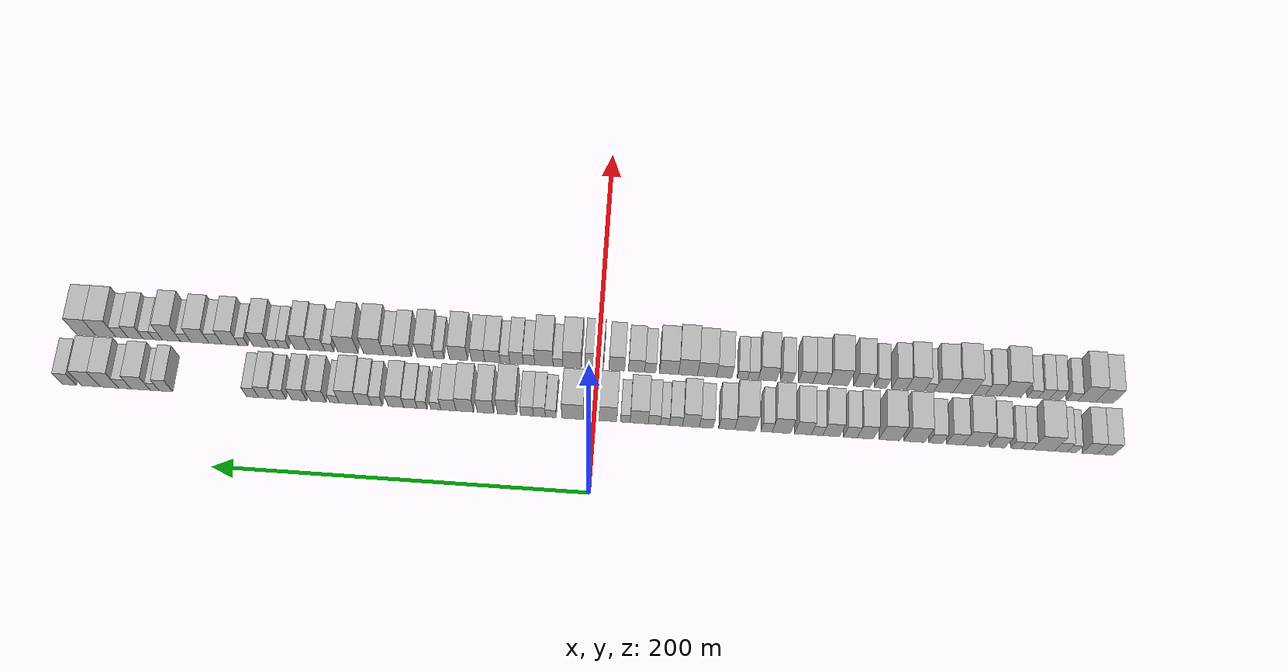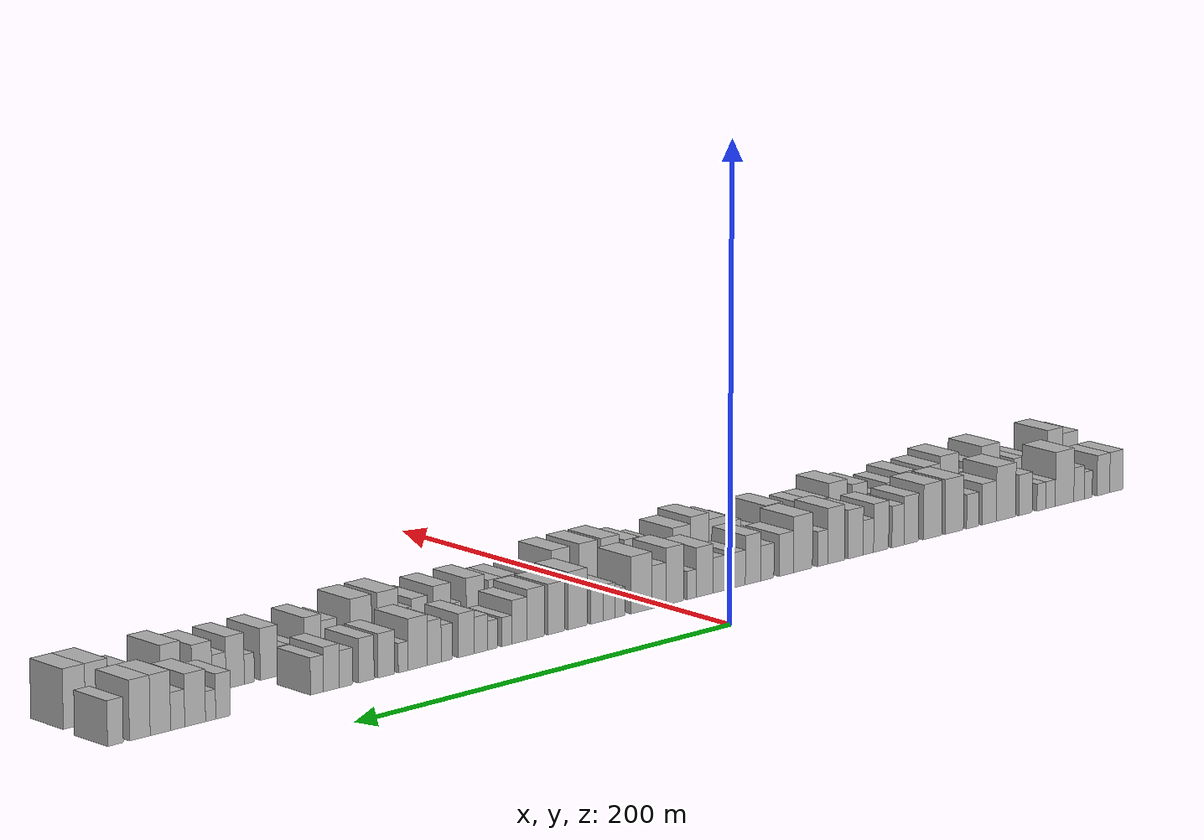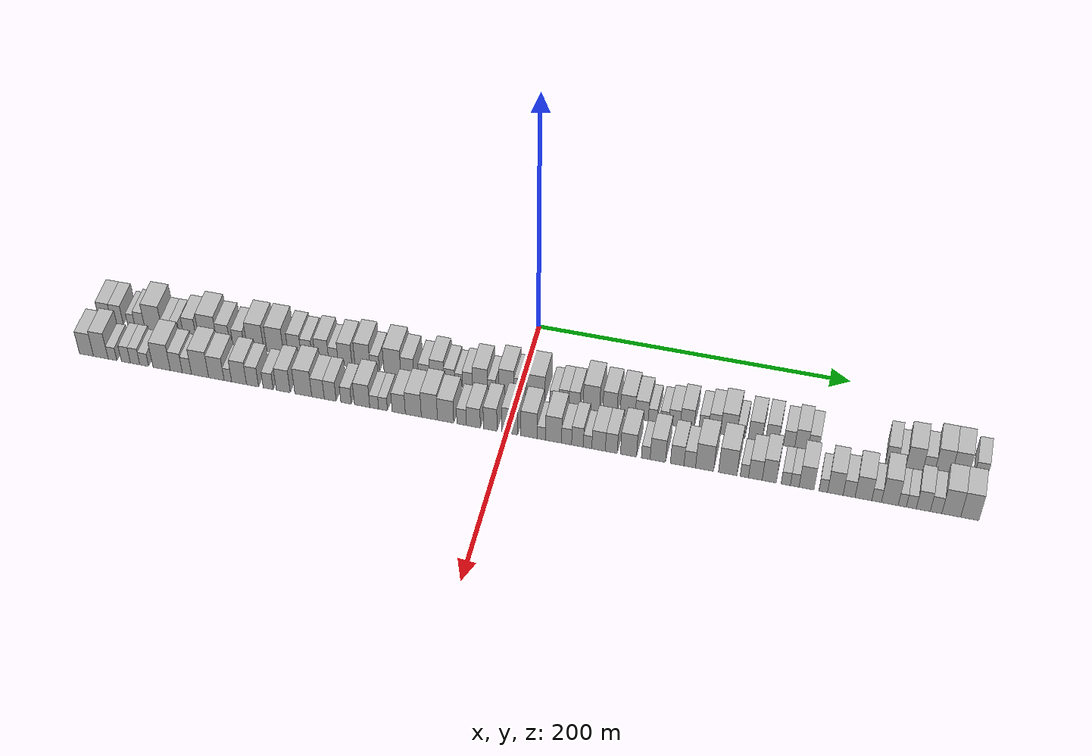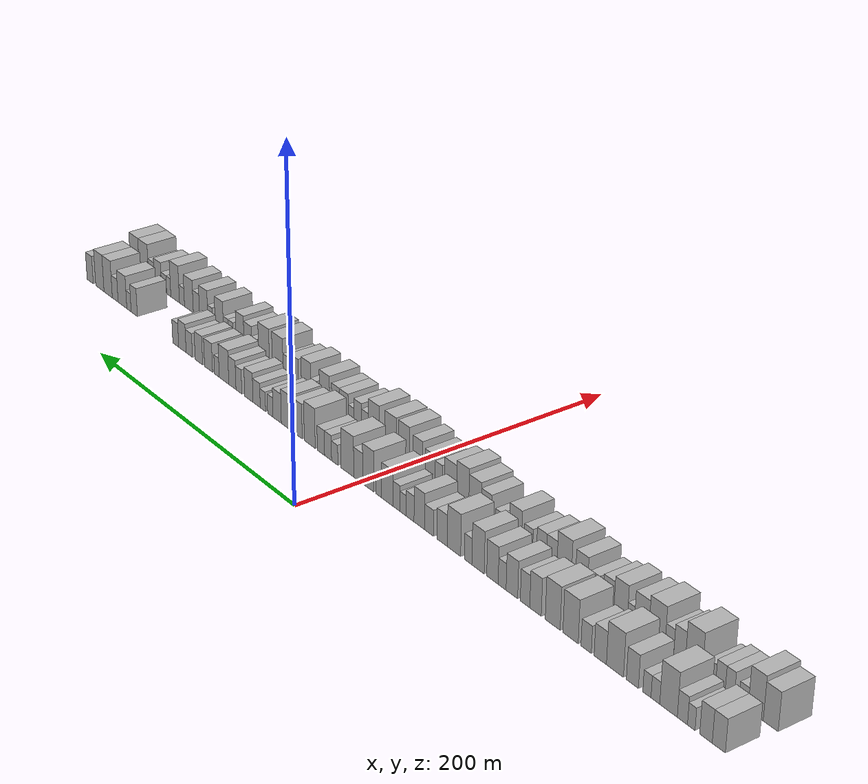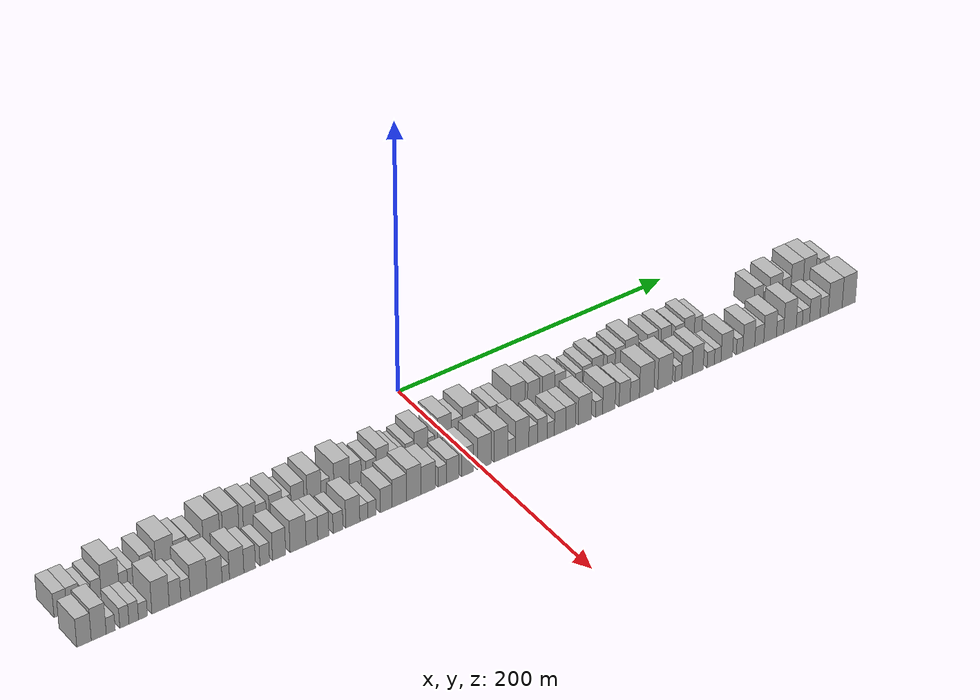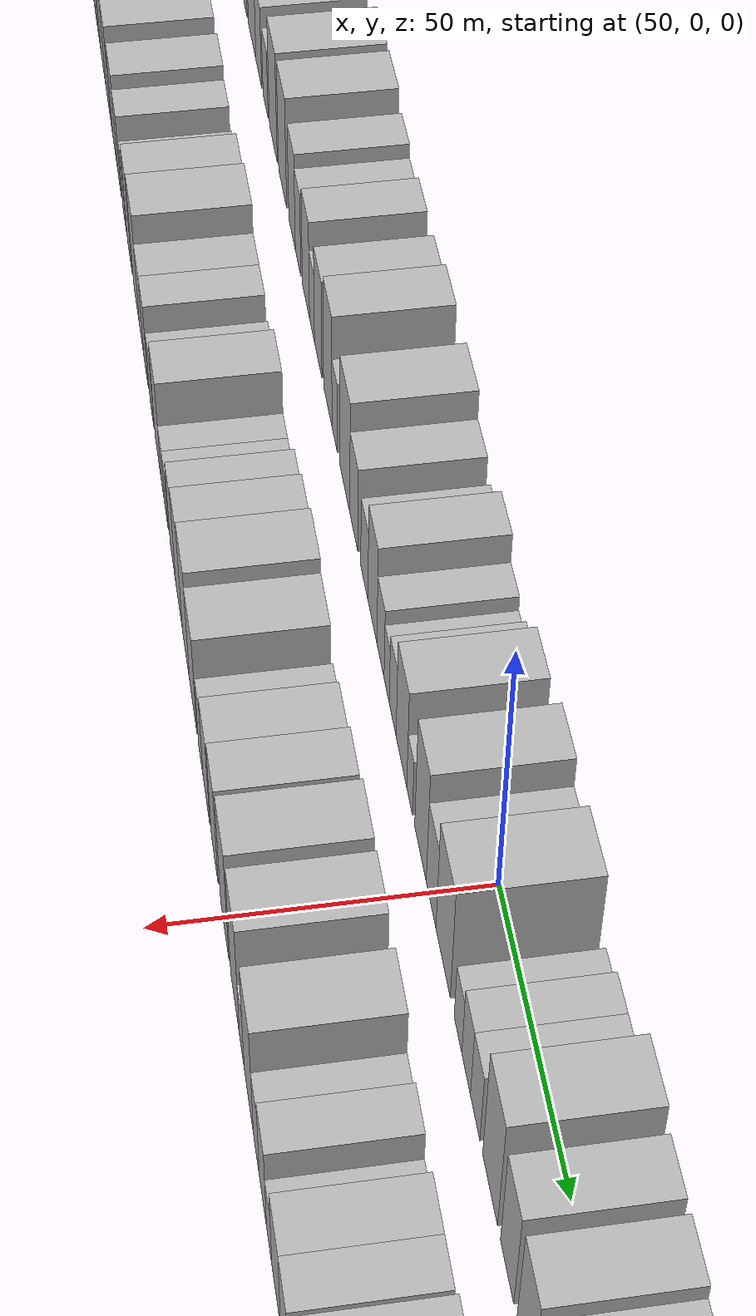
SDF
<sdf version="1.6">
 <world name="default">
  <scene>
   <sky><clouds><speed>12</speed></clouds></sky>
   <ambient>0.4 0.4 0.4 1</ambient>
   <background>0.7 0.7 0.7 1</background>
   <shadows>1</shadows>
  </scene>
  <gravity>0 0 -9.8066</gravity>
  <magnetic_field>6e-06 2.3e-05 -4.2e-05</magnetic_field>
  <physics default="0" name="default_physics" type="ode">
   <ode>
    <solver>
     <type>quick</type>
     <iters>10</iters>
     <sor>1.0</sor>
     <use_dynamic_moi_rescaling>0</use_dynamic_moi_rescaling>
    </solver>
    <constraints>
     <cfm>0</cfm>
     <erp>0.2</erp>
     <contact_max_correcting_vel>100</contact_max_correcting_vel>
     <contact_surface_layer>0.001</contact_surface_layer>
    </constraints>
   </ode>
   <max_step_size>0.004</max_step_size>
   <real_time_factor>1</real_time_factor>
   <real_time_update_rate>250</real_time_update_rate>
  </physics>
  <light name="sun" type="directional">
   <pose>0 0 10 0 0 0</pose>
   <diffuse>0.8 0.8 0.8 1</diffuse>
   <specular>0.2 0.2 0.2 1</specular>
   <attenuation>
    <range>1000</range>
    <constant>0.9</constant>
    <linear>0.01</linear>
    <quadratic>0.001</quadratic>
   </attenuation>
   <direction>-0.5 0.1 -0.9</direction>
  </light>
  <model name="building_1">
   <static>1</static>
   <pose>50.0000 -271.8112 0 0.000000 0.000000 0.000000</pose>
   <link name="link">
    <pose>0 0 9.00 0 0 0</pose>
    <collision name="collision"><geometry><box><size>20.0000 8.3775 18.0000</size></box></geometry></collision>
    <visual name="visual">
     <cast_shadows>0</cast_shadows>
     <geometry><box><size>20.0000 8.3775 18.0000</size></box></geometry>
     <material>
      <script>
       <uri>model://HANNAS_wall/materials/scripts</uri>
       <uri>model://HANNAS_wall/materials/textures</uri>
       <name>vrc/HANNAS_wall</name>
      </script>
     </material>
    </visual>
   </link>
  </model>
  <model name="building_2">
   <static>1</static>
   <pose>50.0000 -263.5821 0 0.000000 0.000000 0.000000</pose>
   <link name="link">
    <pose>0 0 9.00 0 0 0</pose>
    <collision name="collision"><geometry><box><size>20.0000 8.0807 18.0000</size></box></geometry></collision>
    <visual name="visual">
     <cast_shadows>0</cast_shadows>
     <geometry><box><size>20.0000 8.0807 18.0000</size></box></geometry>
     <material>
      <script>
       <uri>model://HANNAS_wall/materials/scripts</uri>
       <uri>model://HANNAS_wall/materials/textures</uri>
       <name>vrc/HANNAS_wall</name>
      </script>
     </material>
    </visual>
   </link>
  </model>
  <model name="building_3">
   <static>1</static>
   <pose>50.0000 -254.0645 0 0.000000 0.000000 0.000000</pose>
   <link name="link">
    <pose>0 0 6.00 0 0 0</pose>
    <collision name="collision"><geometry><box><size>20.0000 4.9545 12.0000</size></box></geometry></collision>
    <visual name="visual">
     <cast_shadows>0</cast_shadows>
     <geometry><box><size>20.0000 4.9545 12.0000</size></box></geometry>
     <material>
      <script>
       <uri>model://HANNAS_wall/materials/scripts</uri>
       <uri>model://HANNAS_wall/materials/textures</uri>
       <name>vrc/HANNAS_wall</name>
      </script>
     </material>
    </visual>
   </link>
  </model>
  <model name="building_4">
   <static>1</static>
   <pose>50.0000 -248.2441 0 0.000000 0.000000 0.000000</pose>
   <link name="link">
    <pose>0 0 7.50 0 0 0</pose>
    <collision name="collision"><geometry><box><size>20.0000 6.6865 15.0000</size></box></geometry></collision>
    <visual name="visual">
     <cast_shadows>0</cast_shadows>
     <geometry><box><size>20.0000 6.6865 15.0000</size></box></geometry>
     <material>
      <script>
       <uri>model://HANNAS_wall/materials/scripts</uri>
       <uri>model://HANNAS_wall/materials/textures</uri>
       <name>vrc/HANNAS_wall</name>
      </script>
     </material>
    </visual>
   </link>
  </model>
  <model name="building_5">
   <static>1</static>
   <pose>50.0000 -239.0377 0 0.000000 0.000000 0.000000</pose>
   <link name="link">
    <pose>0 0 12.00 0 0 0</pose>
    <collision name="collision"><geometry><box><size>20.0000 11.7262 24.0000</size></box></geometry></collision>
    <visual name="visual">
     <cast_shadows>0</cast_shadows>
     <geometry><box><size>20.0000 11.7262 24.0000</size></box></geometry>
     <material>
      <script>
       <uri>model://HANNAS_wall/materials/scripts</uri>
       <uri>model://HANNAS_wall/materials/textures</uri>
       <name>vrc/HANNAS_wall</name>
      </script>
     </material>
    </visual>
   </link>
  </model>
  <model name="building_6">
   <static>1</static>
   <pose>50.0000 -230.2332 0 0.000000 0.000000 0.000000</pose>
   <link name="link">
    <pose>0 0 6.00 0 0 0</pose>
    <collision name="collision"><geometry><box><size>20.0000 5.8830 12.0000</size></box></geometry></collision>
    <visual name="visual">
     <cast_shadows>0</cast_shadows>
     <geometry><box><size>20.0000 5.8830 12.0000</size></box></geometry>
     <material>
      <script>
       <uri>model://HANNAS_wall/materials/scripts</uri>
       <uri>model://HANNAS_wall/materials/textures</uri>
       <name>vrc/HANNAS_wall</name>
      </script>
     </material>
    </visual>
   </link>
  </model>
  <model name="building_7">
   <static>1</static>
   <pose>50.0000 -224.5194 0 0.000000 0.000000 0.000000</pose>
   <link name="link">
    <pose>0 0 6.00 0 0 0</pose>
    <collision name="collision"><geometry><box><size>20.0000 5.5444 12.0000</size></box></geometry></collision>
    <visual name="visual">
     <cast_shadows>0</cast_shadows>
     <geometry><box><size>20.0000 5.5444 12.0000</size></box></geometry>
     <material>
      <script>
       <uri>model://HANNAS_wall/materials/scripts</uri>
       <uri>model://HANNAS_wall/materials/textures</uri>
       <name>vrc/HANNAS_wall</name>
      </script>
     </material>
    </visual>
   </link>
  </model>
  <model name="building_8">
   <static>1</static>
   <pose>50.0000 -214.5819 0 0.000000 0.000000 0.000000</pose>
   <link name="link">
    <pose>0 0 9.00 0 0 0</pose>
    <collision name="collision"><geometry><box><size>20.0000 8.3306 18.0000</size></box></geometry></collision>
    <visual name="visual">
     <cast_shadows>0</cast_shadows>
     <geometry><box><size>20.0000 8.3306 18.0000</size></box></geometry>
     <material>
      <script>
       <uri>model://HANNAS_wall/materials/scripts</uri>
       <uri>model://HANNAS_wall/materials/textures</uri>
       <name>vrc/HANNAS_wall</name>
      </script>
     </material>
    </visual>
   </link>
  </model>
  <model name="building_9">
   <static>1</static>
   <pose>50.0000 -202.4468 0 0.000000 0.000000 0.000000</pose>
   <link name="link">
    <pose>0 0 12.00 0 0 0</pose>
    <collision name="collision"><geometry><box><size>20.0000 11.9398 24.0000</size></box></geometry></collision>
    <visual name="visual">
     <cast_shadows>0</cast_shadows>
     <geometry><box><size>20.0000 11.9398 24.0000</size></box></geometry>
     <material>
      <script>
       <uri>model://HANNAS_wall/materials/scripts</uri>
       <uri>model://HANNAS_wall/materials/textures</uri>
       <name>vrc/HANNAS_wall</name>
      </script>
     </material>
    </visual>
   </link>
  </model>
  <model name="building_10">
   <static>1</static>
   <pose>50.0000 -192.0998 0 0.000000 0.000000 0.000000</pose>
   <link name="link">
    <pose>0 0 9.00 0 0 0</pose>
    <collision name="collision"><geometry><box><size>20.0000 8.7543 18.0000</size></box></geometry></collision>
    <visual name="visual">
     <cast_shadows>0</cast_shadows>
     <geometry><box><size>20.0000 8.7543 18.0000</size></box></geometry>
     <material>
      <script>
       <uri>model://HANNAS_wall/materials/scripts</uri>
       <uri>model://HANNAS_wall/materials/textures</uri>
       <name>vrc/HANNAS_wall</name>
      </script>
     </material>
    </visual>
   </link>
  </model>
  <model name="building_11">
   <static>1</static>
   <pose>50.0000 -182.0048 0 0.000000 0.000000 0.000000</pose>
   <link name="link">
    <pose>0 0 7.50 0 0 0</pose>
    <collision name="collision"><geometry><box><size>20.0000 7.4357 15.0000</size></box></geometry></collision>
    <visual name="visual">
     <cast_shadows>0</cast_shadows>
     <geometry><box><size>20.0000 7.4357 15.0000</size></box></geometry>
     <material>
      <script>
       <uri>model://HANNAS_wall/materials/scripts</uri>
       <uri>model://HANNAS_wall/materials/textures</uri>
       <name>vrc/HANNAS_wall</name>
      </script>
     </material>
    </visual>
   </link>
  </model>
  <model name="building_12">
   <static>1</static>
   <pose>50.0000 -170.6904 0 0.000000 0.000000 0.000000</pose>
   <link name="link">
    <pose>0 0 12.00 0 0 0</pose>
    <collision name="collision"><geometry><box><size>20.0000 11.1929 24.0000</size></box></geometry></collision>
    <visual name="visual">
     <cast_shadows>0</cast_shadows>
     <geometry><box><size>20.0000 11.1929 24.0000</size></box></geometry>
     <material>
      <script>
       <uri>model://HANNAS_wall/materials/scripts</uri>
       <uri>model://HANNAS_wall/materials/textures</uri>
       <name>vrc/HANNAS_wall</name>
      </script>
     </material>
    </visual>
   </link>
  </model>
  <model name="building_13">
   <static>1</static>
   <pose>50.0000 -157.5460 0 0.000000 0.000000 0.000000</pose>
   <link name="link">
    <pose>0 0 12.00 0 0 0</pose>
    <collision name="collision"><geometry><box><size>20.0000 11.0958 24.0000</size></box></geometry></collision>
    <visual name="visual">
     <cast_shadows>0</cast_shadows>
     <geometry><box><size>20.0000 11.0958 24.0000</size></box></geometry>
     <material>
      <script>
       <uri>model://HANNAS_wall/materials/scripts</uri>
       <uri>model://HANNAS_wall/materials/textures</uri>
       <name>vrc/HANNAS_wall</name>
      </script>
     </material>
    </visual>
   </link>
  </model>
  <model name="building_14">
   <static>1</static>
   <pose>50.0000 -144.6521 0 0.000000 0.000000 0.000000</pose>
   <link name="link">
    <pose>0 0 10.50 0 0 0</pose>
    <collision name="collision"><geometry><box><size>20.0000 8.6921 21.0000</size></box></geometry></collision>
    <visual name="visual">
     <cast_shadows>0</cast_shadows>
     <geometry><box><size>20.0000 8.6921 21.0000</size></box></geometry>
     <material>
      <script>
       <uri>model://HANNAS_wall/materials/scripts</uri>
       <uri>model://HANNAS_wall/materials/textures</uri>
       <name>vrc/HANNAS_wall</name>
      </script>
     </material>
    </visual>
   </link>
  </model>
  <model name="building_15">
   <static>1</static>
   <pose>50.0000 -136.6996 0 0.000000 0.000000 0.000000</pose>
   <link name="link">
    <pose>0 0 9.00 0 0 0</pose>
    <collision name="collision"><geometry><box><size>20.0000 7.2128 18.0000</size></box></geometry></collision>
    <visual name="visual">
     <cast_shadows>0</cast_shadows>
     <geometry><box><size>20.0000 7.2128 18.0000</size></box></geometry>
     <material>
      <script>
       <uri>model://HANNAS_wall/materials/scripts</uri>
       <uri>model://HANNAS_wall/materials/textures</uri>
       <name>vrc/HANNAS_wall</name>
      </script>
     </material>
    </visual>
   </link>
  </model>
  <model name="building_16">
   <static>1</static>
   <pose>50.0000 -126.6089 0 0.000000 0.000000 0.000000</pose>
   <link name="link">
    <pose>0 0 10.50 0 0 0</pose>
    <collision name="collision"><geometry><box><size>20.0000 8.9687 21.0000</size></box></geometry></collision>
    <visual name="visual">
     <cast_shadows>0</cast_shadows>
     <geometry><box><size>20.0000 8.9687 21.0000</size></box></geometry>
     <material>
      <script>
       <uri>model://HANNAS_wall/materials/scripts</uri>
       <uri>model://HANNAS_wall/materials/textures</uri>
       <name>vrc/HANNAS_wall</name>
      </script>
     </material>
    </visual>
   </link>
  </model>
  <model name="building_17">
   <static>1</static>
   <pose>50.0000 -119.0434 0 0.000000 0.000000 0.000000</pose>
   <link name="link">
    <pose>0 0 7.50 0 0 0</pose>
    <collision name="collision"><geometry><box><size>20.0000 6.1621 15.0000</size></box></geometry></collision>
    <visual name="visual">
     <cast_shadows>0</cast_shadows>
     <geometry><box><size>20.0000 6.1621 15.0000</size></box></geometry>
     <material>
      <script>
       <uri>model://HANNAS_wall/materials/scripts</uri>
       <uri>model://HANNAS_wall/materials/textures</uri>
       <name>vrc/HANNAS_wall</name>
      </script>
     </material>
    </visual>
   </link>
  </model>
  <model name="building_18">
   <static>1</static>
   <pose>50.0000 -111.4475 0 0.000000 0.000000 0.000000</pose>
   <link name="link">
    <pose>0 0 10.50 0 0 0</pose>
    <collision name="collision"><geometry><box><size>20.0000 9.0298 21.0000</size></box></geometry></collision>
    <visual name="visual">
     <cast_shadows>0</cast_shadows>
     <geometry><box><size>20.0000 9.0298 21.0000</size></box></geometry>
     <material>
      <script>
       <uri>model://HANNAS_wall/materials/scripts</uri>
       <uri>model://HANNAS_wall/materials/textures</uri>
       <name>vrc/HANNAS_wall</name>
      </script>
     </material>
    </visual>
   </link>
  </model>
  <model name="building_19">
   <static>1</static>
   <pose>50.0000 -99.9927 0 0.000000 0.000000 0.000000</pose>
   <link name="link">
    <pose>0 0 12.00 0 0 0</pose>
    <collision name="collision"><geometry><box><size>20.0000 9.8798 24.0000</size></box></geometry></collision>
    <visual name="visual">
     <cast_shadows>0</cast_shadows>
     <geometry><box><size>20.0000 9.8798 24.0000</size></box></geometry>
     <material>
      <script>
       <uri>model://HANNAS_wall/materials/scripts</uri>
       <uri>model://HANNAS_wall/materials/textures</uri>
       <name>vrc/HANNAS_wall</name>
      </script>
     </material>
    </visual>
   </link>
  </model>
  <model name="building_20">
   <static>1</static>
   <pose>50.0000 -92.0321 0 0.000000 0.000000 0.000000</pose>
   <link name="link">
    <pose>0 0 7.50 0 0 0</pose>
    <collision name="collision"><geometry><box><size>20.0000 6.0414 15.0000</size></box></geometry></collision>
    <visual name="visual">
     <cast_shadows>0</cast_shadows>
     <geometry><box><size>20.0000 6.0414 15.0000</size></box></geometry>
     <material>
      <script>
       <uri>model://HANNAS_wall/materials/scripts</uri>
       <uri>model://HANNAS_wall/materials/textures</uri>
       <name>vrc/HANNAS_wall</name>
      </script>
     </material>
    </visual>
   </link>
  </model>
  <model name="building_21">
   <static>1</static>
   <pose>50.0000 -80.5241 0 0.000000 0.000000 0.000000</pose>
   <link name="link">
    <pose>0 0 12.00 0 0 0</pose>
    <collision name="collision"><geometry><box><size>20.0000 10.9745 24.0000</size></box></geometry></collision>
    <visual name="visual">
     <cast_shadows>0</cast_shadows>
     <geometry><box><size>20.0000 10.9745 24.0000</size></box></geometry>
     <material>
      <script>
       <uri>model://HANNAS_wall/materials/scripts</uri>
       <uri>model://HANNAS_wall/materials/textures</uri>
       <name>vrc/HANNAS_wall</name>
      </script>
     </material>
    </visual>
   </link>
  </model>
  <model name="building_22">
   <static>1</static>
   <pose>50.0000 -70.8118 0 0.000000 0.000000 0.000000</pose>
   <link name="link">
    <pose>0 0 9.00 0 0 0</pose>
    <collision name="collision"><geometry><box><size>20.0000 8.4502 18.0000</size></box></geometry></collision>
    <visual name="visual">
     <cast_shadows>0</cast_shadows>
     <geometry><box><size>20.0000 8.4502 18.0000</size></box></geometry>
     <material>
      <script>
       <uri>model://HANNAS_wall/materials/scripts</uri>
       <uri>model://HANNAS_wall/materials/textures</uri>
       <name>vrc/HANNAS_wall</name>
      </script>
     </material>
    </visual>
   </link>
  </model>
  <model name="building_23">
   <static>1</static>
   <pose>50.0000 -59.8838 0 0.000000 0.000000 0.000000</pose>
   <link name="link">
    <pose>0 0 7.50 0 0 0</pose>
    <collision name="collision"><geometry><box><size>20.0000 7.4058 15.0000</size></box></geometry></collision>
    <visual name="visual">
     <cast_shadows>0</cast_shadows>
     <geometry><box><size>20.0000 7.4058 15.0000</size></box></geometry>
     <material>
      <script>
       <uri>model://HANNAS_wall/materials/scripts</uri>
       <uri>model://HANNAS_wall/materials/textures</uri>
       <name>vrc/HANNAS_wall</name>
      </script>
     </material>
    </visual>
   </link>
  </model>
  <model name="building_24">
   <static>1</static>
   <pose>50.0000 -51.6690 0 0.000000 0.000000 0.000000</pose>
   <link name="link">
    <pose>0 0 10.50 0 0 0</pose>
    <collision name="collision"><geometry><box><size>20.0000 9.0238 21.0000</size></box></geometry></collision>
    <visual name="visual">
     <cast_shadows>0</cast_shadows>
     <geometry><box><size>20.0000 9.0238 21.0000</size></box></geometry>
     <material>
      <script>
       <uri>model://HANNAS_wall/materials/scripts</uri>
       <uri>model://HANNAS_wall/materials/textures</uri>
       <name>vrc/HANNAS_wall</name>
      </script>
     </material>
    </visual>
   </link>
  </model>
  <model name="building_25">
   <static>1</static>
   <pose>50.0000 -43.6620 0 0.000000 0.000000 0.000000</pose>
   <link name="link">
    <pose>0 0 7.50 0 0 0</pose>
    <collision name="collision"><geometry><box><size>20.0000 6.9903 15.0000</size></box></geometry></collision>
    <visual name="visual">
     <cast_shadows>0</cast_shadows>
     <geometry><box><size>20.0000 6.9903 15.0000</size></box></geometry>
     <material>
      <script>
       <uri>model://HANNAS_wall/materials/scripts</uri>
       <uri>model://HANNAS_wall/materials/textures</uri>
       <name>vrc/HANNAS_wall</name>
      </script>
     </material>
    </visual>
   </link>
  </model>
  <model name="building_26">
   <static>1</static>
   <pose>50.0000 -37.7205 0 0.000000 0.000000 0.000000</pose>
   <link name="link">
    <pose>0 0 6.00 0 0 0</pose>
    <collision name="collision"><geometry><box><size>20.0000 4.8926 12.0000</size></box></geometry></collision>
    <visual name="visual">
     <cast_shadows>0</cast_shadows>
     <geometry><box><size>20.0000 4.8926 12.0000</size></box></geometry>
     <material>
      <script>
       <uri>model://HANNAS_wall/materials/scripts</uri>
       <uri>model://HANNAS_wall/materials/textures</uri>
       <name>vrc/HANNAS_wall</name>
      </script>
     </material>
    </visual>
   </link>
  </model>
  <model name="building_27">
   <static>1</static>
   <pose>50.0000 -32.0515 0 0.000000 0.000000 0.000000</pose>
   <link name="link">
    <pose>0 0 7.50 0 0 0</pose>
    <collision name="collision"><geometry><box><size>20.0000 6.4454 15.0000</size></box></geometry></collision>
    <visual name="visual">
     <cast_shadows>0</cast_shadows>
     <geometry><box><size>20.0000 6.4454 15.0000</size></box></geometry>
     <material>
      <script>
       <uri>model://HANNAS_wall/materials/scripts</uri>
       <uri>model://HANNAS_wall/materials/textures</uri>
       <name>vrc/HANNAS_wall</name>
      </script>
     </material>
    </visual>
   </link>
  </model>
  <model name="building_28">
   <static>1</static>
   <pose>50.0000 -23.9721 0 0.000000 0.000000 0.000000</pose>
   <link name="link">
    <pose>0 0 10.50 0 0 0</pose>
    <collision name="collision"><geometry><box><size>20.0000 9.7133 21.0000</size></box></geometry></collision>
    <visual name="visual">
     <cast_shadows>0</cast_shadows>
     <geometry><box><size>20.0000 9.7133 21.0000</size></box></geometry>
     <material>
      <script>
       <uri>model://HANNAS_wall/materials/scripts</uri>
       <uri>model://HANNAS_wall/materials/textures</uri>
       <name>vrc/HANNAS_wall</name>
      </script>
     </material>
    </visual>
   </link>
  </model>
  <model name="building_29">
   <static>1</static>
   <pose>50.0000 -16.5725 0 0.000000 0.000000 0.000000</pose>
   <link name="link">
    <pose>0 0 6.00 0 0 0</pose>
    <collision name="collision"><geometry><box><size>20.0000 5.0859 12.0000</size></box></geometry></collision>
    <visual name="visual">
     <cast_shadows>0</cast_shadows>
     <geometry><box><size>20.0000 5.0859 12.0000</size></box></geometry>
     <material>
      <script>
       <uri>model://HANNAS_wall/materials/scripts</uri>
       <uri>model://HANNAS_wall/materials/textures</uri>
       <name>vrc/HANNAS_wall</name>
      </script>
     </material>
    </visual>
   </link>
  </model>
  <model name="building_30">
   <static>1</static>
   <pose>50.0000 -7.0902 0 0.000000 0.000000 0.000000</pose>
   <link name="link">
    <pose>0 0 12.00 0 0 0</pose>
    <collision name="collision"><geometry><box><size>20.0000 9.8788 24.0000</size></box></geometry></collision>
    <visual name="visual">
     <cast_shadows>0</cast_shadows>
     <geometry><box><size>20.0000 9.8788 24.0000</size></box></geometry>
     <material>
      <script>
       <uri>model://HANNAS_wall/materials/scripts</uri>
       <uri>model://HANNAS_wall/materials/textures</uri>
       <name>vrc/HANNAS_wall</name>
      </script>
     </material>
    </visual>
   </link>
  </model>
  <model name="building_31">
   <static>1</static>
   <pose>50.0000 1.8893 0 0.000000 0.000000 0.000000</pose>
   <link name="link">
    <pose>0 0 9.00 0 0 0</pose>
    <collision name="collision"><geometry><box><size>20.0000 8.0801 18.0000</size></box></geometry></collision>
    <visual name="visual">
     <cast_shadows>0</cast_shadows>
     <geometry><box><size>20.0000 8.0801 18.0000</size></box></geometry>
     <material>
      <script>
       <uri>model://HANNAS_wall/materials/scripts</uri>
       <uri>model://HANNAS_wall/materials/textures</uri>
       <name>vrc/HANNAS_wall</name>
      </script>
     </material>
    </visual>
   </link>
  </model>
  <model name="building_32">
   <static>1</static>
   <pose>50.0000 11.7142 0 0.000000 0.000000 0.000000</pose>
   <link name="link">
    <pose>0 0 12.00 0 0 0</pose>
    <collision name="collision"><geometry><box><size>20.0000 11.5697 24.0000</size></box></geometry></collision>
    <visual name="visual">
     <cast_shadows>0</cast_shadows>
     <geometry><box><size>20.0000 11.5697 24.0000</size></box></geometry>
     <material>
      <script>
       <uri>model://HANNAS_wall/materials/scripts</uri>
       <uri>model://HANNAS_wall/materials/textures</uri>
       <name>vrc/HANNAS_wall</name>
      </script>
     </material>
    </visual>
   </link>
  </model>
  <model name="building_33">
   <static>1</static>
   <pose>50.0000 23.4167 0 0.000000 0.000000 0.000000</pose>
   <link name="link">
    <pose>0 0 6.00 0 0 0</pose>
    <collision name="collision"><geometry><box><size>20.0000 5.8353 12.0000</size></box></geometry></collision>
    <visual name="visual">
     <cast_shadows>0</cast_shadows>
     <geometry><box><size>20.0000 5.8353 12.0000</size></box></geometry>
     <material>
      <script>
       <uri>model://HANNAS_wall/materials/scripts</uri>
       <uri>model://HANNAS_wall/materials/textures</uri>
       <name>vrc/HANNAS_wall</name>
      </script>
     </material>
    </visual>
   </link>
  </model>
  <model name="building_34">
   <static>1</static>
   <pose>50.0000 29.5625 0 0.000000 0.000000 0.000000</pose>
   <link name="link">
    <pose>0 0 7.50 0 0 0</pose>
    <collision name="collision"><geometry><box><size>20.0000 6.4564 15.0000</size></box></geometry></collision>
    <visual name="visual">
     <cast_shadows>0</cast_shadows>
     <geometry><box><size>20.0000 6.4564 15.0000</size></box></geometry>
     <material>
      <script>
       <uri>model://HANNAS_wall/materials/scripts</uri>
       <uri>model://HANNAS_wall/materials/textures</uri>
       <name>vrc/HANNAS_wall</name>
      </script>
     </material>
    </visual>
   </link>
  </model>
  <model name="building_35">
   <static>1</static>
   <pose>50.0000 36.2377 0 0.000000 0.000000 0.000000</pose>
   <link name="link">
    <pose>0 0 7.50 0 0 0</pose>
    <collision name="collision"><geometry><box><size>20.0000 6.8939 15.0000</size></box></geometry></collision>
    <visual name="visual">
     <cast_shadows>0</cast_shadows>
     <geometry><box><size>20.0000 6.8939 15.0000</size></box></geometry>
     <material>
      <script>
       <uri>model://HANNAS_wall/materials/scripts</uri>
       <uri>model://HANNAS_wall/materials/textures</uri>
       <name>vrc/HANNAS_wall</name>
      </script>
     </material>
    </visual>
   </link>
  </model>
  <model name="building_36">
   <static>1</static>
   <pose>50.0000 46.8793 0 0.000000 0.000000 0.000000</pose>
   <link name="link">
    <pose>0 0 12.00 0 0 0</pose>
    <collision name="collision"><geometry><box><size>20.0000 10.3893 24.0000</size></box></geometry></collision>
    <visual name="visual">
     <cast_shadows>0</cast_shadows>
     <geometry><box><size>20.0000 10.3893 24.0000</size></box></geometry>
     <material>
      <script>
       <uri>model://HANNAS_wall/materials/scripts</uri>
       <uri>model://HANNAS_wall/materials/textures</uri>
       <name>vrc/HANNAS_wall</name>
      </script>
     </material>
    </visual>
   </link>
  </model>
  <model name="building_37">
   <static>1</static>
   <pose>50.0000 58.5164 0 0.000000 0.000000 0.000000</pose>
   <link name="link">
    <pose>0 0 10.50 0 0 0</pose>
    <collision name="collision"><geometry><box><size>20.0000 8.8849 21.0000</size></box></geometry></collision>
    <visual name="visual">
     <cast_shadows>0</cast_shadows>
     <geometry><box><size>20.0000 8.8849 21.0000</size></box></geometry>
     <material>
      <script>
       <uri>model://HANNAS_wall/materials/scripts</uri>
       <uri>model://HANNAS_wall/materials/textures</uri>
       <name>vrc/HANNAS_wall</name>
      </script>
     </material>
    </visual>
   </link>
  </model>
  <model name="building_38">
   <static>1</static>
   <pose>50.0000 69.6701 0 0.000000 0.000000 0.000000</pose>
   <link name="link">
    <pose>0 0 10.50 0 0 0</pose>
    <collision name="collision"><geometry><box><size>20.0000 9.4225 21.0000</size></box></geometry></collision>
    <visual name="visual">
     <cast_shadows>0</cast_shadows>
     <geometry><box><size>20.0000 9.4225 21.0000</size></box></geometry>
     <material>
      <script>
       <uri>model://HANNAS_wall/materials/scripts</uri>
       <uri>model://HANNAS_wall/materials/textures</uri>
       <name>vrc/HANNAS_wall</name>
      </script>
     </material>
    </visual>
   </link>
  </model>
  <model name="building_39">
   <static>1</static>
   <pose>50.0000 78.4824 0 0.000000 0.000000 0.000000</pose>
   <link name="link">
    <pose>0 0 9.00 0 0 0</pose>
    <collision name="collision"><geometry><box><size>20.0000 8.2021 18.0000</size></box></geometry></collision>
    <visual name="visual">
     <cast_shadows>0</cast_shadows>
     <geometry><box><size>20.0000 8.2021 18.0000</size></box></geometry>
     <material>
      <script>
       <uri>model://HANNAS_wall/materials/scripts</uri>
       <uri>model://HANNAS_wall/materials/textures</uri>
       <name>vrc/HANNAS_wall</name>
      </script>
     </material>
    </visual>
   </link>
  </model>
  <model name="building_40">
   <static>1</static>
   <pose>50.0000 85.2810 0 0.000000 0.000000 0.000000</pose>
   <link name="link">
    <pose>0 0 6.00 0 0 0</pose>
    <collision name="collision"><geometry><box><size>20.0000 5.3951 12.0000</size></box></geometry></collision>
    <visual name="visual">
     <cast_shadows>0</cast_shadows>
     <geometry><box><size>20.0000 5.3951 12.0000</size></box></geometry>
     <material>
      <script>
       <uri>model://HANNAS_wall/materials/scripts</uri>
       <uri>model://HANNAS_wall/materials/textures</uri>
       <name>vrc/HANNAS_wall</name>
      </script>
     </material>
    </visual>
   </link>
  </model>
  <model name="building_41">
   <static>1</static>
   <pose>50.0000 92.6717 0 0.000000 0.000000 0.000000</pose>
   <link name="link">
    <pose>0 0 6.00 0 0 0</pose>
    <collision name="collision"><geometry><box><size>20.0000 5.3864 12.0000</size></box></geometry></collision>
    <visual name="visual">
     <cast_shadows>0</cast_shadows>
     <geometry><box><size>20.0000 5.3864 12.0000</size></box></geometry>
     <material>
      <script>
       <uri>model://HANNAS_wall/materials/scripts</uri>
       <uri>model://HANNAS_wall/materials/textures</uri>
       <name>vrc/HANNAS_wall</name>
      </script>
     </material>
    </visual>
   </link>
  </model>
  <model name="building_42">
   <static>1</static>
   <pose>50.0000 98.9908 0 0.000000 0.000000 0.000000</pose>
   <link name="link">
    <pose>0 0 7.50 0 0 0</pose>
    <collision name="collision"><geometry><box><size>20.0000 7.2517 15.0000</size></box></geometry></collision>
    <visual name="visual">
     <cast_shadows>0</cast_shadows>
     <geometry><box><size>20.0000 7.2517 15.0000</size></box></geometry>
     <material>
      <script>
       <uri>model://HANNAS_wall/materials/scripts</uri>
       <uri>model://HANNAS_wall/materials/textures</uri>
       <name>vrc/HANNAS_wall</name>
      </script>
     </material>
    </visual>
   </link>
  </model>
  <model name="building_43">
   <static>1</static>
   <pose>50.0000 106.8519 0 0.000000 0.000000 0.000000</pose>
   <link name="link">
    <pose>0 0 9.00 0 0 0</pose>
    <collision name="collision"><geometry><box><size>20.0000 8.4705 18.0000</size></box></geometry></collision>
    <visual name="visual">
     <cast_shadows>0</cast_shadows>
     <geometry><box><size>20.0000 8.4705 18.0000</size></box></geometry>
     <material>
      <script>
       <uri>model://HANNAS_wall/materials/scripts</uri>
       <uri>model://HANNAS_wall/materials/textures</uri>
       <name>vrc/HANNAS_wall</name>
      </script>
     </material>
    </visual>
   </link>
  </model>
  <model name="building_44">
   <static>1</static>
   <pose>50.0000 117.1174 0 0.000000 0.000000 0.000000</pose>
   <link name="link">
    <pose>0 0 7.50 0 0 0</pose>
    <collision name="collision"><geometry><box><size>20.0000 6.0605 15.0000</size></box></geometry></collision>
    <visual name="visual">
     <cast_shadows>0</cast_shadows>
     <geometry><box><size>20.0000 6.0605 15.0000</size></box></geometry>
     <material>
      <script>
       <uri>model://HANNAS_wall/materials/scripts</uri>
       <uri>model://HANNAS_wall/materials/textures</uri>
       <name>vrc/HANNAS_wall</name>
      </script>
     </material>
    </visual>
   </link>
  </model>
  <model name="building_45">
   <static>1</static>
   <pose>50.0000 123.8608 0 0.000000 0.000000 0.000000</pose>
   <link name="link">
    <pose>0 0 9.00 0 0 0</pose>
    <collision name="collision"><geometry><box><size>20.0000 7.4264 18.0000</size></box></geometry></collision>
    <visual name="visual">
     <cast_shadows>0</cast_shadows>
     <geometry><box><size>20.0000 7.4264 18.0000</size></box></geometry>
     <material>
      <script>
       <uri>model://HANNAS_wall/materials/scripts</uri>
       <uri>model://HANNAS_wall/materials/textures</uri>
       <name>vrc/HANNAS_wall</name>
      </script>
     </material>
    </visual>
   </link>
  </model>
  <model name="building_46">
   <static>1</static>
   <pose>50.0000 132.5873 0 0.000000 0.000000 0.000000</pose>
   <link name="link">
    <pose>0 0 10.50 0 0 0</pose>
    <collision name="collision"><geometry><box><size>20.0000 10.0266 21.0000</size></box></geometry></collision>
    <visual name="visual">
     <cast_shadows>0</cast_shadows>
     <geometry><box><size>20.0000 10.0266 21.0000</size></box></geometry>
     <material>
      <script>
       <uri>model://HANNAS_wall/materials/scripts</uri>
       <uri>model://HANNAS_wall/materials/textures</uri>
       <name>vrc/HANNAS_wall</name>
      </script>
     </material>
    </visual>
   </link>
  </model>
  <model name="building_47">
   <static>1</static>
   <pose>50.0000 140.1266 0 0.000000 0.000000 0.000000</pose>
   <link name="link">
    <pose>0 0 6.00 0 0 0</pose>
    <collision name="collision"><geometry><box><size>20.0000 5.0519 12.0000</size></box></geometry></collision>
    <visual name="visual">
     <cast_shadows>0</cast_shadows>
     <geometry><box><size>20.0000 5.0519 12.0000</size></box></geometry>
     <material>
      <script>
       <uri>model://HANNAS_wall/materials/scripts</uri>
       <uri>model://HANNAS_wall/materials/textures</uri>
       <name>vrc/HANNAS_wall</name>
      </script>
     </material>
    </visual>
   </link>
  </model>
  <model name="building_48">
   <static>1</static>
   <pose>50.0000 148.9408 0 0.000000 0.000000 0.000000</pose>
   <link name="link">
    <pose>0 0 9.00 0 0 0</pose>
    <collision name="collision"><geometry><box><size>20.0000 8.5766 18.0000</size></box></geometry></collision>
    <visual name="visual">
     <cast_shadows>0</cast_shadows>
     <geometry><box><size>20.0000 8.5766 18.0000</size></box></geometry>
     <material>
      <script>
       <uri>model://HANNAS_wall/materials/scripts</uri>
       <uri>model://HANNAS_wall/materials/textures</uri>
       <name>vrc/HANNAS_wall</name>
      </script>
     </material>
    </visual>
   </link>
  </model>
  <model name="building_49">
   <static>1</static>
   <pose>50.0000 159.2718 0 0.000000 0.000000 0.000000</pose>
   <link name="link">
    <pose>0 0 9.00 0 0 0</pose>
    <collision name="collision"><geometry><box><size>20.0000 8.0853 18.0000</size></box></geometry></collision>
    <visual name="visual">
     <cast_shadows>0</cast_shadows>
     <geometry><box><size>20.0000 8.0853 18.0000</size></box></geometry>
     <material>
      <script>
       <uri>model://HANNAS_wall/materials/scripts</uri>
       <uri>model://HANNAS_wall/materials/textures</uri>
       <name>vrc/HANNAS_wall</name>
      </script>
     </material>
    </visual>
   </link>
  </model>
  <model name="building_50">
   <static>1</static>
   <pose>50.0000 169.7689 0 0.000000 0.000000 0.000000</pose>
   <link name="link">
    <pose>0 0 7.50 0 0 0</pose>
    <collision name="collision"><geometry><box><size>20.0000 6.9091 15.0000</size></box></geometry></collision>
    <visual name="visual">
     <cast_shadows>0</cast_shadows>
     <geometry><box><size>20.0000 6.9091 15.0000</size></box></geometry>
     <material>
      <script>
       <uri>model://HANNAS_wall/materials/scripts</uri>
       <uri>model://HANNAS_wall/materials/textures</uri>
       <name>vrc/HANNAS_wall</name>
      </script>
     </material>
    </visual>
   </link>
  </model>
  <model name="building_51">
   <static>1</static>
   <pose>50.0000 177.2824 0 0.000000 0.000000 0.000000</pose>
   <link name="link">
    <pose>0 0 9.00 0 0 0</pose>
    <collision name="collision"><geometry><box><size>20.0000 8.1179 18.0000</size></box></geometry></collision>
    <visual name="visual">
     <cast_shadows>0</cast_shadows>
     <geometry><box><size>20.0000 8.1179 18.0000</size></box></geometry>
     <material>
      <script>
       <uri>model://HANNAS_wall/materials/scripts</uri>
       <uri>model://HANNAS_wall/materials/textures</uri>
       <name>vrc/HANNAS_wall</name>
      </script>
     </material>
    </visual>
   </link>
  </model>
  <model name="building_52">
   <static>1</static>
   <pose>50.0000 184.6182 0 0.000000 0.000000 0.000000</pose>
   <link name="link">
    <pose>0 0 7.50 0 0 0</pose>
    <collision name="collision"><geometry><box><size>20.0000 6.5537 15.0000</size></box></geometry></collision>
    <visual name="visual">
     <cast_shadows>0</cast_shadows>
     <geometry><box><size>20.0000 6.5537 15.0000</size></box></geometry>
     <material>
      <script>
       <uri>model://HANNAS_wall/materials/scripts</uri>
       <uri>model://HANNAS_wall/materials/textures</uri>
       <name>vrc/HANNAS_wall</name>
      </script>
     </material>
    </visual>
   </link>
  </model>
  <model name="building_53">
   <static>1</static>
   <pose>50.0000 231.8629 0 0.000000 0.000000 0.000000</pose>
   <link name="link">
    <pose>0 0 9.00 0 0 0</pose>
    <collision name="collision"><geometry><box><size>20.0000 7.3119 18.0000</size></box></geometry></collision>
    <visual name="visual">
     <cast_shadows>0</cast_shadows>
     <geometry><box><size>20.0000 7.3119 18.0000</size></box></geometry>
     <material>
      <script>
       <uri>model://HANNAS_wall/materials/scripts</uri>
       <uri>model://HANNAS_wall/materials/textures</uri>
       <name>vrc/HANNAS_wall</name>
      </script>
     </material>
    </visual>
   </link>
  </model>
  <model name="building_54">
   <static>1</static>
   <pose>50.0000 238.0434 0 0.000000 0.000000 0.000000</pose>
   <link name="link">
    <pose>0 0 6.00 0 0 0</pose>
    <collision name="collision"><geometry><box><size>20.0000 5.0492 12.0000</size></box></geometry></collision>
    <visual name="visual">
     <cast_shadows>0</cast_shadows>
     <geometry><box><size>20.0000 5.0492 12.0000</size></box></geometry>
     <material>
      <script>
       <uri>model://HANNAS_wall/materials/scripts</uri>
       <uri>model://HANNAS_wall/materials/textures</uri>
       <name>vrc/HANNAS_wall</name>
      </script>
     </material>
    </visual>
   </link>
  </model>
  <model name="building_55">
   <static>1</static>
   <pose>50.0000 245.7052 0 0.000000 0.000000 0.000000</pose>
   <link name="link">
    <pose>0 0 10.50 0 0 0</pose>
    <collision name="collision"><geometry><box><size>20.0000 10.2743 21.0000</size></box></geometry></collision>
    <visual name="visual">
     <cast_shadows>0</cast_shadows>
     <geometry><box><size>20.0000 10.2743 21.0000</size></box></geometry>
     <material>
      <script>
       <uri>model://HANNAS_wall/materials/scripts</uri>
       <uri>model://HANNAS_wall/materials/textures</uri>
       <name>vrc/HANNAS_wall</name>
      </script>
     </material>
    </visual>
   </link>
  </model>
  <model name="building_56">
   <static>1</static>
   <pose>50.0000 254.3147 0 0.000000 0.000000 0.000000</pose>
   <link name="link">
    <pose>0 0 7.50 0 0 0</pose>
    <collision name="collision"><geometry><box><size>20.0000 6.9448 15.0000</size></box></geometry></collision>
    <visual name="visual">
     <cast_shadows>0</cast_shadows>
     <geometry><box><size>20.0000 6.9448 15.0000</size></box></geometry>
     <material>
      <script>
       <uri>model://HANNAS_wall/materials/scripts</uri>
       <uri>model://HANNAS_wall/materials/textures</uri>
       <name>vrc/HANNAS_wall</name>
      </script>
     </material>
    </visual>
   </link>
  </model>
  <model name="building_57">
   <static>1</static>
   <pose>50.0000 262.7760 0 0.000000 0.000000 0.000000</pose>
   <link name="link">
    <pose>0 0 12.00 0 0 0</pose>
    <collision name="collision"><geometry><box><size>20.0000 9.9779 24.0000</size></box></geometry></collision>
    <visual name="visual">
     <cast_shadows>0</cast_shadows>
     <geometry><box><size>20.0000 9.9779 24.0000</size></box></geometry>
     <material>
      <script>
       <uri>model://HANNAS_wall/materials/scripts</uri>
       <uri>model://HANNAS_wall/materials/textures</uri>
       <name>vrc/HANNAS_wall</name>
      </script>
     </material>
    </visual>
   </link>
  </model>
  <model name="building_58">
   <static>1</static>
   <pose>50.0000 272.8071 0 0.000000 0.000000 0.000000</pose>
   <link name="link">
    <pose>0 0 12.00 0 0 0</pose>
    <collision name="collision"><geometry><box><size>20.0000 10.0843 24.0000</size></box></geometry></collision>
    <visual name="visual">
     <cast_shadows>0</cast_shadows>
     <geometry><box><size>20.0000 10.0843 24.0000</size></box></geometry>
     <material>
      <script>
       <uri>model://HANNAS_wall/materials/scripts</uri>
       <uri>model://HANNAS_wall/materials/textures</uri>
       <name>vrc/HANNAS_wall</name>
      </script>
     </material>
    </visual>
   </link>
  </model>
  <model name="building_59">
   <static>1</static>
   <pose>50.0000 284.6481 0 0.000000 0.000000 0.000000</pose>
   <link name="link">
    <pose>0 0 9.00 0 0 0</pose>
    <collision name="collision"><geometry><box><size>20.0000 7.5978 18.0000</size></box></geometry></collision>
    <visual name="visual">
     <cast_shadows>0</cast_shadows>
     <geometry><box><size>20.0000 7.5978 18.0000</size></box></geometry>
     <material>
      <script>
       <uri>model://HANNAS_wall/materials/scripts</uri>
       <uri>model://HANNAS_wall/materials/textures</uri>
       <name>vrc/HANNAS_wall</name>
      </script>
     </material>
    </visual>
   </link>
  </model>
  <model name="building_60">
   <static>1</static>
   <pose>79.0000 -273.2672 0 0.000000 0.000000 0.000000</pose>
   <link name="link">
    <pose>0 0 10.50 0 0 0</pose>
    <collision name="collision"><geometry><box><size>20.0000 9.4655 21.0000</size></box></geometry></collision>
    <visual name="visual">
     <cast_shadows>0</cast_shadows>
     <geometry><box><size>20.0000 9.4655 21.0000</size></box></geometry>
     <material>
      <script>
       <uri>model://HANNAS_wall/materials/scripts</uri>
       <uri>model://HANNAS_wall/materials/textures</uri>
       <name>vrc/HANNAS_wall</name>
      </script>
     </material>
    </visual>
   </link>
  </model>
  <model name="building_61">
   <static>1</static>
   <pose>79.0000 -263.6652 0 0.000000 0.000000 0.000000</pose>
   <link name="link">
    <pose>0 0 12.00 0 0 0</pose>
    <collision name="collision"><geometry><box><size>20.0000 9.7386 24.0000</size></box></geometry></collision>
    <visual name="visual">
     <cast_shadows>0</cast_shadows>
     <geometry><box><size>20.0000 9.7386 24.0000</size></box></geometry>
     <material>
      <script>
       <uri>model://HANNAS_wall/materials/scripts</uri>
       <uri>model://HANNAS_wall/materials/textures</uri>
       <name>vrc/HANNAS_wall</name>
      </script>
     </material>
    </visual>
   </link>
  </model>
  <model name="building_62">
   <static>1</static>
   <pose>79.0000 -255.8377 0 0.000000 0.000000 0.000000</pose>
   <link name="link">
    <pose>0 0 6.00 0 0 0</pose>
    <collision name="collision"><geometry><box><size>20.0000 5.9163 12.0000</size></box></geometry></collision>
    <visual name="visual">
     <cast_shadows>0</cast_shadows>
     <geometry><box><size>20.0000 5.9163 12.0000</size></box></geometry>
     <material>
      <script>
       <uri>model://HANNAS_wall/materials/scripts</uri>
       <uri>model://HANNAS_wall/materials/textures</uri>
       <name>vrc/HANNAS_wall</name>
      </script>
     </material>
    </visual>
   </link>
  </model>
  <model name="building_63">
   <static>1</static>
   <pose>79.0000 -246.8693 0 0.000000 0.000000 0.000000</pose>
   <link name="link">
    <pose>0 0 7.50 0 0 0</pose>
    <collision name="collision"><geometry><box><size>20.0000 6.0205 15.0000</size></box></geometry></collision>
    <visual name="visual">
     <cast_shadows>0</cast_shadows>
     <geometry><box><size>20.0000 6.0205 15.0000</size></box></geometry>
     <material>
      <script>
       <uri>model://HANNAS_wall/materials/scripts</uri>
       <uri>model://HANNAS_wall/materials/textures</uri>
       <name>vrc/HANNAS_wall</name>
      </script>
     </material>
    </visual>
   </link>
  </model>
  <model name="building_64">
   <static>1</static>
   <pose>79.0000 -240.7284 0 0.000000 0.000000 0.000000</pose>
   <link name="link">
    <pose>0 0 7.50 0 0 0</pose>
    <collision name="collision"><geometry><box><size>20.0000 6.2613 15.0000</size></box></geometry></collision>
    <visual name="visual">
     <cast_shadows>0</cast_shadows>
     <geometry><box><size>20.0000 6.2613 15.0000</size></box></geometry>
     <material>
      <script>
       <uri>model://HANNAS_wall/materials/scripts</uri>
       <uri>model://HANNAS_wall/materials/textures</uri>
       <name>vrc/HANNAS_wall</name>
      </script>
     </material>
    </visual>
   </link>
  </model>
  <model name="building_65">
   <static>1</static>
   <pose>79.0000 -234.6587 0 0.000000 0.000000 0.000000</pose>
   <link name="link">
    <pose>0 0 6.00 0 0 0</pose>
    <collision name="collision"><geometry><box><size>20.0000 5.8780 12.0000</size></box></geometry></collision>
    <visual name="visual">
     <cast_shadows>0</cast_shadows>
     <geometry><box><size>20.0000 5.8780 12.0000</size></box></geometry>
     <material>
      <script>
       <uri>model://HANNAS_wall/materials/scripts</uri>
       <uri>model://HANNAS_wall/materials/textures</uri>
       <name>vrc/HANNAS_wall</name>
      </script>
     </material>
    </visual>
   </link>
  </model>
  <model name="building_66">
   <static>1</static>
   <pose>79.0000 -222.9857 0 0.000000 0.000000 0.000000</pose>
   <link name="link">
    <pose>0 0 12.00 0 0 0</pose>
    <collision name="collision"><geometry><box><size>20.0000 11.4681 24.0000</size></box></geometry></collision>
    <visual name="visual">
     <cast_shadows>0</cast_shadows>
     <geometry><box><size>20.0000 11.4681 24.0000</size></box></geometry>
     <material>
      <script>
       <uri>model://HANNAS_wall/materials/scripts</uri>
       <uri>model://HANNAS_wall/materials/textures</uri>
       <name>vrc/HANNAS_wall</name>
      </script>
     </material>
    </visual>
   </link>
  </model>
  <model name="building_67">
   <static>1</static>
   <pose>79.0000 -213.2998 0 0.000000 0.000000 0.000000</pose>
   <link name="link">
    <pose>0 0 9.00 0 0 0</pose>
    <collision name="collision"><geometry><box><size>20.0000 7.9037 18.0000</size></box></geometry></collision>
    <visual name="visual">
     <cast_shadows>0</cast_shadows>
     <geometry><box><size>20.0000 7.9037 18.0000</size></box></geometry>
     <material>
      <script>
       <uri>model://HANNAS_wall/materials/scripts</uri>
       <uri>model://HANNAS_wall/materials/textures</uri>
       <name>vrc/HANNAS_wall</name>
      </script>
     </material>
    </visual>
   </link>
  </model>
  <model name="building_68">
   <static>1</static>
   <pose>79.0000 -206.2962 0 0.000000 0.000000 0.000000</pose>
   <link name="link">
    <pose>0 0 7.50 0 0 0</pose>
    <collision name="collision"><geometry><box><size>20.0000 6.1034 15.0000</size></box></geometry></collision>
    <visual name="visual">
     <cast_shadows>0</cast_shadows>
     <geometry><box><size>20.0000 6.1034 15.0000</size></box></geometry>
     <material>
      <script>
       <uri>model://HANNAS_wall/materials/scripts</uri>
       <uri>model://HANNAS_wall/materials/textures</uri>
       <name>vrc/HANNAS_wall</name>
      </script>
     </material>
    </visual>
   </link>
  </model>
  <model name="building_69">
   <static>1</static>
   <pose>79.0000 -197.5754 0 0.000000 0.000000 0.000000</pose>
   <link name="link">
    <pose>0 0 12.00 0 0 0</pose>
    <collision name="collision"><geometry><box><size>20.0000 11.3381 24.0000</size></box></geometry></collision>
    <visual name="visual">
     <cast_shadows>0</cast_shadows>
     <geometry><box><size>20.0000 11.3381 24.0000</size></box></geometry>
     <material>
      <script>
       <uri>model://HANNAS_wall/materials/scripts</uri>
       <uri>model://HANNAS_wall/materials/textures</uri>
       <name>vrc/HANNAS_wall</name>
      </script>
     </material>
    </visual>
   </link>
  </model>
  <model name="building_70">
   <static>1</static>
   <pose>79.0000 -186.7995 0 0.000000 0.000000 0.000000</pose>
   <link name="link">
    <pose>0 0 10.50 0 0 0</pose>
    <collision name="collision"><geometry><box><size>20.0000 10.2138 21.0000</size></box></geometry></collision>
    <visual name="visual">
     <cast_shadows>0</cast_shadows>
     <geometry><box><size>20.0000 10.2138 21.0000</size></box></geometry>
     <material>
      <script>
       <uri>model://HANNAS_wall/materials/scripts</uri>
       <uri>model://HANNAS_wall/materials/textures</uri>
       <name>vrc/HANNAS_wall</name>
      </script>
     </material>
    </visual>
   </link>
  </model>
  <model name="building_71">
   <static>1</static>
   <pose>79.0000 -179.2257 0 0.000000 0.000000 0.000000</pose>
   <link name="link">
    <pose>0 0 6.00 0 0 0</pose>
    <collision name="collision"><geometry><box><size>20.0000 4.9337 12.0000</size></box></geometry></collision>
    <visual name="visual">
     <cast_shadows>0</cast_shadows>
     <geometry><box><size>20.0000 4.9337 12.0000</size></box></geometry>
     <material>
      <script>
       <uri>model://HANNAS_wall/materials/scripts</uri>
       <uri>model://HANNAS_wall/materials/textures</uri>
       <name>vrc/HANNAS_wall</name>
      </script>
     </material>
    </visual>
   </link>
  </model>
  <model name="building_72">
   <static>1</static>
   <pose>79.0000 -171.8806 0 0.000000 0.000000 0.000000</pose>
   <link name="link">
    <pose>0 0 10.50 0 0 0</pose>
    <collision name="collision"><geometry><box><size>20.0000 9.7565 21.0000</size></box></geometry></collision>
    <visual name="visual">
     <cast_shadows>0</cast_shadows>
     <geometry><box><size>20.0000 9.7565 21.0000</size></box></geometry>
     <material>
      <script>
       <uri>model://HANNAS_wall/materials/scripts</uri>
       <uri>model://HANNAS_wall/materials/textures</uri>
       <name>vrc/HANNAS_wall</name>
      </script>
     </material>
    </visual>
   </link>
  </model>
  <model name="building_73">
   <static>1</static>
   <pose>79.0000 -163.0456 0 0.000000 0.000000 0.000000</pose>
   <link name="link">
    <pose>0 0 9.00 0 0 0</pose>
    <collision name="collision"><geometry><box><size>20.0000 7.9136 18.0000</size></box></geometry></collision>
    <visual name="visual">
     <cast_shadows>0</cast_shadows>
     <geometry><box><size>20.0000 7.9136 18.0000</size></box></geometry>
     <material>
      <script>
       <uri>model://HANNAS_wall/materials/scripts</uri>
       <uri>model://HANNAS_wall/materials/textures</uri>
       <name>vrc/HANNAS_wall</name>
      </script>
     </material>
    </visual>
   </link>
  </model>
  <model name="building_74">
   <static>1</static>
   <pose>79.0000 -152.8099 0 0.000000 0.000000 0.000000</pose>
   <link name="link">
    <pose>0 0 7.50 0 0 0</pose>
    <collision name="collision"><geometry><box><size>20.0000 6.5578 15.0000</size></box></geometry></collision>
    <visual name="visual">
     <cast_shadows>0</cast_shadows>
     <geometry><box><size>20.0000 6.5578 15.0000</size></box></geometry>
     <material>
      <script>
       <uri>model://HANNAS_wall/materials/scripts</uri>
       <uri>model://HANNAS_wall/materials/textures</uri>
       <name>vrc/HANNAS_wall</name>
      </script>
     </material>
    </visual>
   </link>
  </model>
  <model name="building_75">
   <static>1</static>
   <pose>79.0000 -142.9900 0 0.000000 0.000000 0.000000</pose>
   <link name="link">
    <pose>0 0 10.50 0 0 0</pose>
    <collision name="collision"><geometry><box><size>20.0000 9.0820 21.0000</size></box></geometry></collision>
    <visual name="visual">
     <cast_shadows>0</cast_shadows>
     <geometry><box><size>20.0000 9.0820 21.0000</size></box></geometry>
     <material>
      <script>
       <uri>model://HANNAS_wall/materials/scripts</uri>
       <uri>model://HANNAS_wall/materials/textures</uri>
       <name>vrc/HANNAS_wall</name>
      </script>
     </material>
    </visual>
   </link>
  </model>
  <model name="building_76">
   <static>1</static>
   <pose>79.0000 -129.9418 0 0.000000 0.000000 0.000000</pose>
   <link name="link">
    <pose>0 0 12.00 0 0 0</pose>
    <collision name="collision"><geometry><box><size>20.0000 11.0143 24.0000</size></box></geometry></collision>
    <visual name="visual">
     <cast_shadows>0</cast_shadows>
     <geometry><box><size>20.0000 11.0143 24.0000</size></box></geometry>
     <material>
      <script>
       <uri>model://HANNAS_wall/materials/scripts</uri>
       <uri>model://HANNAS_wall/materials/textures</uri>
       <name>vrc/HANNAS_wall</name>
      </script>
     </material>
    </visual>
   </link>
  </model>
  <model name="building_77">
   <static>1</static>
   <pose>79.0000 -120.3730 0 0.000000 0.000000 0.000000</pose>
   <link name="link">
    <pose>0 0 9.00 0 0 0</pose>
    <collision name="collision"><geometry><box><size>20.0000 8.1234 18.0000</size></box></geometry></collision>
    <visual name="visual">
     <cast_shadows>0</cast_shadows>
     <geometry><box><size>20.0000 8.1234 18.0000</size></box></geometry>
     <material>
      <script>
       <uri>model://HANNAS_wall/materials/scripts</uri>
       <uri>model://HANNAS_wall/materials/textures</uri>
       <name>vrc/HANNAS_wall</name>
      </script>
     </material>
    </visual>
   </link>
  </model>
  <model name="building_78">
   <static>1</static>
   <pose>79.0000 -112.4714 0 0.000000 0.000000 0.000000</pose>
   <link name="link">
    <pose>0 0 9.00 0 0 0</pose>
    <collision name="collision"><geometry><box><size>20.0000 7.6798 18.0000</size></box></geometry></collision>
    <visual name="visual">
     <cast_shadows>0</cast_shadows>
     <geometry><box><size>20.0000 7.6798 18.0000</size></box></geometry>
     <material>
      <script>
       <uri>model://HANNAS_wall/materials/scripts</uri>
       <uri>model://HANNAS_wall/materials/textures</uri>
       <name>vrc/HANNAS_wall</name>
      </script>
     </material>
    </visual>
   </link>
  </model>
  <model name="building_79">
   <static>1</static>
   <pose>79.0000 -102.2353 0 0.000000 0.000000 0.000000</pose>
   <link name="link">
    <pose>0 0 7.50 0 0 0</pose>
    <collision name="collision"><geometry><box><size>20.0000 6.7924 15.0000</size></box></geometry></collision>
    <visual name="visual">
     <cast_shadows>0</cast_shadows>
     <geometry><box><size>20.0000 6.7924 15.0000</size></box></geometry>
     <material>
      <script>
       <uri>model://HANNAS_wall/materials/scripts</uri>
       <uri>model://HANNAS_wall/materials/textures</uri>
       <name>vrc/HANNAS_wall</name>
      </script>
     </material>
    </visual>
   </link>
  </model>
  <model name="building_80">
   <static>1</static>
   <pose>79.0000 -91.9015 0 0.000000 0.000000 0.000000</pose>
   <link name="link">
    <pose>0 0 10.50 0 0 0</pose>
    <collision name="collision"><geometry><box><size>20.0000 9.8751 21.0000</size></box></geometry></collision>
    <visual name="visual">
     <cast_shadows>0</cast_shadows>
     <geometry><box><size>20.0000 9.8751 21.0000</size></box></geometry>
     <material>
      <script>
       <uri>model://HANNAS_wall/materials/scripts</uri>
       <uri>model://HANNAS_wall/materials/textures</uri>
       <name>vrc/HANNAS_wall</name>
      </script>
     </material>
    </visual>
   </link>
  </model>
  <model name="building_81">
   <static>1</static>
   <pose>79.0000 -84.1158 0 0.000000 0.000000 0.000000</pose>
   <link name="link">
    <pose>0 0 6.00 0 0 0</pose>
    <collision name="collision"><geometry><box><size>20.0000 5.6962 12.0000</size></box></geometry></collision>
    <visual name="visual">
     <cast_shadows>0</cast_shadows>
     <geometry><box><size>20.0000 5.6962 12.0000</size></box></geometry>
     <material>
      <script>
       <uri>model://HANNAS_wall/materials/scripts</uri>
       <uri>model://HANNAS_wall/materials/textures</uri>
       <name>vrc/HANNAS_wall</name>
      </script>
     </material>
    </visual>
   </link>
  </model>
  <model name="building_82">
   <static>1</static>
   <pose>79.0000 -78.4565 0 0.000000 0.000000 0.000000</pose>
   <link name="link">
    <pose>0 0 6.00 0 0 0</pose>
    <collision name="collision"><geometry><box><size>20.0000 5.6225 12.0000</size></box></geometry></collision>
    <visual name="visual">
     <cast_shadows>0</cast_shadows>
     <geometry><box><size>20.0000 5.6225 12.0000</size></box></geometry>
     <material>
      <script>
       <uri>model://HANNAS_wall/materials/scripts</uri>
       <uri>model://HANNAS_wall/materials/textures</uri>
       <name>vrc/HANNAS_wall</name>
      </script>
     </material>
    </visual>
   </link>
  </model>
  <model name="building_83">
   <static>1</static>
   <pose>79.0000 -68.4065 0 0.000000 0.000000 0.000000</pose>
   <link name="link">
    <pose>0 0 9.00 0 0 0</pose>
    <collision name="collision"><geometry><box><size>20.0000 8.4775 18.0000</size></box></geometry></collision>
    <visual name="visual">
     <cast_shadows>0</cast_shadows>
     <geometry><box><size>20.0000 8.4775 18.0000</size></box></geometry>
     <material>
      <script>
       <uri>model://HANNAS_wall/materials/scripts</uri>
       <uri>model://HANNAS_wall/materials/textures</uri>
       <name>vrc/HANNAS_wall</name>
      </script>
     </material>
    </visual>
   </link>
  </model>
  <model name="building_84">
   <static>1</static>
   <pose>79.0000 -59.0621 0 0.000000 0.000000 0.000000</pose>
   <link name="link">
    <pose>0 0 10.50 0 0 0</pose>
    <collision name="collision"><geometry><box><size>20.0000 10.2111 21.0000</size></box></geometry></collision>
    <visual name="visual">
     <cast_shadows>0</cast_shadows>
     <geometry><box><size>20.0000 10.2111 21.0000</size></box></geometry>
     <material>
      <script>
       <uri>model://HANNAS_wall/materials/scripts</uri>
       <uri>model://HANNAS_wall/materials/textures</uri>
       <name>vrc/HANNAS_wall</name>
      </script>
     </material>
    </visual>
   </link>
  </model>
  <model name="building_85">
   <static>1</static>
   <pose>79.0000 -48.8124 0 0.000000 0.000000 0.000000</pose>
   <link name="link">
    <pose>0 0 12.00 0 0 0</pose>
    <collision name="collision"><geometry><box><size>20.0000 10.2884 24.0000</size></box></geometry></collision>
    <visual name="visual">
     <cast_shadows>0</cast_shadows>
     <geometry><box><size>20.0000 10.2884 24.0000</size></box></geometry>
     <material>
      <script>
       <uri>model://HANNAS_wall/materials/scripts</uri>
       <uri>model://HANNAS_wall/materials/textures</uri>
       <name>vrc/HANNAS_wall</name>
      </script>
     </material>
    </visual>
   </link>
  </model>
  <model name="building_86">
   <static>1</static>
   <pose>79.0000 -38.5170 0 0.000000 0.000000 0.000000</pose>
   <link name="link">
    <pose>0 0 10.50 0 0 0</pose>
    <collision name="collision"><geometry><box><size>20.0000 10.3025 21.0000</size></box></geometry></collision>
    <visual name="visual">
     <cast_shadows>0</cast_shadows>
     <geometry><box><size>20.0000 10.3025 21.0000</size></box></geometry>
     <material>
      <script>
       <uri>model://HANNAS_wall/materials/scripts</uri>
       <uri>model://HANNAS_wall/materials/textures</uri>
       <name>vrc/HANNAS_wall</name>
      </script>
     </material>
    </visual>
   </link>
  </model>
  <model name="building_87">
   <static>1</static>
   <pose>79.0000 -28.3432 0 0.000000 0.000000 0.000000</pose>
   <link name="link">
    <pose>0 0 7.50 0 0 0</pose>
    <collision name="collision"><geometry><box><size>20.0000 6.0449 15.0000</size></box></geometry></collision>
    <visual name="visual">
     <cast_shadows>0</cast_shadows>
     <geometry><box><size>20.0000 6.0449 15.0000</size></box></geometry>
     <material>
      <script>
       <uri>model://HANNAS_wall/materials/scripts</uri>
       <uri>model://HANNAS_wall/materials/textures</uri>
       <name>vrc/HANNAS_wall</name>
      </script>
     </material>
    </visual>
   </link>
  </model>
  <model name="building_88">
   <static>1</static>
   <pose>79.0000 -20.9120 0 0.000000 0.000000 0.000000</pose>
   <link name="link">
    <pose>0 0 9.00 0 0 0</pose>
    <collision name="collision"><geometry><box><size>20.0000 8.8177 18.0000</size></box></geometry></collision>
    <visual name="visual">
     <cast_shadows>0</cast_shadows>
     <geometry><box><size>20.0000 8.8177 18.0000</size></box></geometry>
     <material>
      <script>
       <uri>model://HANNAS_wall/materials/scripts</uri>
       <uri>model://HANNAS_wall/materials/textures</uri>
       <name>vrc/HANNAS_wall</name>
      </script>
     </material>
    </visual>
   </link>
  </model>
  <model name="building_89">
   <static>1</static>
   <pose>79.0000 -10.2408 0 0.000000 0.000000 0.000000</pose>
   <link name="link">
    <pose>0 0 10.50 0 0 0</pose>
    <collision name="collision"><geometry><box><size>20.0000 8.5247 21.0000</size></box></geometry></collision>
    <visual name="visual">
     <cast_shadows>0</cast_shadows>
     <geometry><box><size>20.0000 8.5247 21.0000</size></box></geometry>
     <material>
      <script>
       <uri>model://HANNAS_wall/materials/scripts</uri>
       <uri>model://HANNAS_wall/materials/textures</uri>
       <name>vrc/HANNAS_wall</name>
      </script>
     </material>
    </visual>
   </link>
  </model>
  <model name="building_90">
   <static>1</static>
   <pose>79.0000 2.0427 0 0.000000 0.000000 0.000000</pose>
   <link name="link">
    <pose>0 0 12.00 0 0 0</pose>
    <collision name="collision"><geometry><box><size>20.0000 10.0423 24.0000</size></box></geometry></collision>
    <visual name="visual">
     <cast_shadows>0</cast_shadows>
     <geometry><box><size>20.0000 10.0423 24.0000</size></box></geometry>
     <material>
      <script>
       <uri>model://HANNAS_wall/materials/scripts</uri>
       <uri>model://HANNAS_wall/materials/textures</uri>
       <name>vrc/HANNAS_wall</name>
      </script>
     </material>
    </visual>
   </link>
  </model>
  <model name="building_91">
   <static>1</static>
   <pose>79.0000 14.1333 0 0.000000 0.000000 0.000000</pose>
   <link name="link">
    <pose>0 0 12.00 0 0 0</pose>
    <collision name="collision"><geometry><box><size>20.0000 10.1388 24.0000</size></box></geometry></collision>
    <visual name="visual">
     <cast_shadows>0</cast_shadows>
     <geometry><box><size>20.0000 10.1388 24.0000</size></box></geometry>
     <material>
      <script>
       <uri>model://HANNAS_wall/materials/scripts</uri>
       <uri>model://HANNAS_wall/materials/textures</uri>
       <name>vrc/HANNAS_wall</name>
      </script>
     </material>
    </visual>
   </link>
  </model>
  <model name="building_92">
   <static>1</static>
   <pose>79.0000 21.8661 0 0.000000 0.000000 0.000000</pose>
   <link name="link">
    <pose>0 0 6.00 0 0 0</pose>
    <collision name="collision"><geometry><box><size>20.0000 5.3268 12.0000</size></box></geometry></collision>
    <visual name="visual">
     <cast_shadows>0</cast_shadows>
     <geometry><box><size>20.0000 5.3268 12.0000</size></box></geometry>
     <material>
      <script>
       <uri>model://HANNAS_wall/materials/scripts</uri>
       <uri>model://HANNAS_wall/materials/textures</uri>
       <name>vrc/HANNAS_wall</name>
      </script>
     </material>
    </visual>
   </link>
  </model>
  <model name="building_93">
   <static>1</static>
   <pose>79.0000 29.5009 0 0.000000 0.000000 0.000000</pose>
   <link name="link">
    <pose>0 0 12.00 0 0 0</pose>
    <collision name="collision"><geometry><box><size>20.0000 9.9429 24.0000</size></box></geometry></collision>
    <visual name="visual">
     <cast_shadows>0</cast_shadows>
     <geometry><box><size>20.0000 9.9429 24.0000</size></box></geometry>
     <material>
      <script>
       <uri>model://HANNAS_wall/materials/scripts</uri>
       <uri>model://HANNAS_wall/materials/textures</uri>
       <name>vrc/HANNAS_wall</name>
      </script>
     </material>
    </visual>
   </link>
  </model>
  <model name="building_94">
   <static>1</static>
   <pose>79.0000 37.6089 0 0.000000 0.000000 0.000000</pose>
   <link name="link">
    <pose>0 0 7.50 0 0 0</pose>
    <collision name="collision"><geometry><box><size>20.0000 6.2732 15.0000</size></box></geometry></collision>
    <visual name="visual">
     <cast_shadows>0</cast_shadows>
     <geometry><box><size>20.0000 6.2732 15.0000</size></box></geometry>
     <material>
      <script>
       <uri>model://HANNAS_wall/materials/scripts</uri>
       <uri>model://HANNAS_wall/materials/textures</uri>
       <name>vrc/HANNAS_wall</name>
      </script>
     </material>
    </visual>
   </link>
  </model>
  <model name="building_95">
   <static>1</static>
   <pose>79.0000 44.4142 0 0.000000 0.000000 0.000000</pose>
   <link name="link">
    <pose>0 0 9.00 0 0 0</pose>
    <collision name="collision"><geometry><box><size>20.0000 7.3374 18.0000</size></box></geometry></collision>
    <visual name="visual">
     <cast_shadows>0</cast_shadows>
     <geometry><box><size>20.0000 7.3374 18.0000</size></box></geometry>
     <material>
      <script>
       <uri>model://HANNAS_wall/materials/scripts</uri>
       <uri>model://HANNAS_wall/materials/textures</uri>
       <name>vrc/HANNAS_wall</name>
      </script>
     </material>
    </visual>
   </link>
  </model>
  <model name="building_96">
   <static>1</static>
   <pose>79.0000 50.7081 0 0.000000 0.000000 0.000000</pose>
   <link name="link">
    <pose>0 0 6.00 0 0 0</pose>
    <collision name="collision"><geometry><box><size>20.0000 5.2504 12.0000</size></box></geometry></collision>
    <visual name="visual">
     <cast_shadows>0</cast_shadows>
     <geometry><box><size>20.0000 5.2504 12.0000</size></box></geometry>
     <material>
      <script>
       <uri>model://HANNAS_wall/materials/scripts</uri>
       <uri>model://HANNAS_wall/materials/textures</uri>
       <name>vrc/HANNAS_wall</name>
      </script>
     </material>
    </visual>
   </link>
  </model>
  <model name="building_97">
   <static>1</static>
   <pose>79.0000 57.5254 0 0.000000 0.000000 0.000000</pose>
   <link name="link">
    <pose>0 0 9.00 0 0 0</pose>
    <collision name="collision"><geometry><box><size>20.0000 8.3843 18.0000</size></box></geometry></collision>
    <visual name="visual">
     <cast_shadows>0</cast_shadows>
     <geometry><box><size>20.0000 8.3843 18.0000</size></box></geometry>
     <material>
      <script>
       <uri>model://HANNAS_wall/materials/scripts</uri>
       <uri>model://HANNAS_wall/materials/textures</uri>
       <name>vrc/HANNAS_wall</name>
      </script>
     </material>
    </visual>
   </link>
  </model>
  <model name="building_98">
   <static>1</static>
   <pose>79.0000 65.3954 0 0.000000 0.000000 0.000000</pose>
   <link name="link">
    <pose>0 0 9.00 0 0 0</pose>
    <collision name="collision"><geometry><box><size>20.0000 7.3556 18.0000</size></box></geometry></collision>
    <visual name="visual">
     <cast_shadows>0</cast_shadows>
     <geometry><box><size>20.0000 7.3556 18.0000</size></box></geometry>
     <material>
      <script>
       <uri>model://HANNAS_wall/materials/scripts</uri>
       <uri>model://HANNAS_wall/materials/textures</uri>
       <name>vrc/HANNAS_wall</name>
      </script>
     </material>
    </visual>
   </link>
  </model>
  <model name="building_99">
   <static>1</static>
   <pose>79.0000 76.0162 0 0.000000 0.000000 0.000000</pose>
   <link name="link">
    <pose>0 0 10.50 0 0 0</pose>
    <collision name="collision"><geometry><box><size>20.0000 9.8861 21.0000</size></box></geometry></collision>
    <visual name="visual">
     <cast_shadows>0</cast_shadows>
     <geometry><box><size>20.0000 9.8861 21.0000</size></box></geometry>
     <material>
      <script>
       <uri>model://HANNAS_wall/materials/scripts</uri>
       <uri>model://HANNAS_wall/materials/textures</uri>
       <name>vrc/HANNAS_wall</name>
      </script>
     </material>
    </visual>
   </link>
  </model>
  <model name="building_100">
   <static>1</static>
   <pose>79.0000 86.6463 0 0.000000 0.000000 0.000000</pose>
   <link name="link">
    <pose>0 0 6.00 0 0 0</pose>
    <collision name="collision"><geometry><box><size>20.0000 5.3741 12.0000</size></box></geometry></collision>
    <visual name="visual">
     <cast_shadows>0</cast_shadows>
     <geometry><box><size>20.0000 5.3741 12.0000</size></box></geometry>
     <material>
      <script>
       <uri>model://HANNAS_wall/materials/scripts</uri>
       <uri>model://HANNAS_wall/materials/textures</uri>
       <name>vrc/HANNAS_wall</name>
      </script>
     </material>
    </visual>
   </link>
  </model>
  <model name="building_101">
   <static>1</static>
   <pose>79.0000 94.0636 0 0.000000 0.000000 0.000000</pose>
   <link name="link">
    <pose>0 0 10.50 0 0 0</pose>
    <collision name="collision"><geometry><box><size>20.0000 9.4604 21.0000</size></box></geometry></collision>
    <visual name="visual">
     <cast_shadows>0</cast_shadows>
     <geometry><box><size>20.0000 9.4604 21.0000</size></box></geometry>
     <material>
      <script>
       <uri>model://HANNAS_wall/materials/scripts</uri>
       <uri>model://HANNAS_wall/materials/textures</uri>
       <name>vrc/HANNAS_wall</name>
      </script>
     </material>
    </visual>
   </link>
  </model>
  <model name="building_102">
   <static>1</static>
   <pose>79.0000 105.9681 0 0.000000 0.000000 0.000000</pose>
   <link name="link">
    <pose>0 0 9.00 0 0 0</pose>
    <collision name="collision"><geometry><box><size>20.0000 8.3485 18.0000</size></box></geometry></collision>
    <visual name="visual">
     <cast_shadows>0</cast_shadows>
     <geometry><box><size>20.0000 8.3485 18.0000</size></box></geometry>
     <material>
      <script>
       <uri>model://HANNAS_wall/materials/scripts</uri>
       <uri>model://HANNAS_wall/materials/textures</uri>
       <name>vrc/HANNAS_wall</name>
      </script>
     </material>
    </visual>
   </link>
  </model>
  <model name="building_103">
   <static>1</static>
   <pose>79.0000 113.6608 0 0.000000 0.000000 0.000000</pose>
   <link name="link">
    <pose>0 0 7.50 0 0 0</pose>
    <collision name="collision"><geometry><box><size>20.0000 7.0369 15.0000</size></box></geometry></collision>
    <visual name="visual">
     <cast_shadows>0</cast_shadows>
     <geometry><box><size>20.0000 7.0369 15.0000</size></box></geometry>
     <material>
      <script>
       <uri>model://HANNAS_wall/materials/scripts</uri>
       <uri>model://HANNAS_wall/materials/textures</uri>
       <name>vrc/HANNAS_wall</name>
      </script>
     </material>
    </visual>
   </link>
  </model>
  <model name="building_104">
   <static>1</static>
   <pose>79.0000 122.7035 0 0.000000 0.000000 0.000000</pose>
   <link name="link">
    <pose>0 0 12.00 0 0 0</pose>
    <collision name="collision"><geometry><box><size>20.0000 11.0485 24.0000</size></box></geometry></collision>
    <visual name="visual">
     <cast_shadows>0</cast_shadows>
     <geometry><box><size>20.0000 11.0485 24.0000</size></box></geometry>
     <material>
      <script>
       <uri>model://HANNAS_wall/materials/scripts</uri>
       <uri>model://HANNAS_wall/materials/textures</uri>
       <name>vrc/HANNAS_wall</name>
      </script>
     </material>
    </visual>
   </link>
  </model>
  <model name="building_105">
   <static>1</static>
   <pose>79.0000 136.8146 0 0.000000 0.000000 0.000000</pose>
   <link name="link">
    <pose>0 0 12.00 0 0 0</pose>
    <collision name="collision"><geometry><box><size>20.0000 11.1739 24.0000</size></box></geometry></collision>
    <visual name="visual">
     <cast_shadows>0</cast_shadows>
     <geometry><box><size>20.0000 11.1739 24.0000</size></box></geometry>
     <material>
      <script>
       <uri>model://HANNAS_wall/materials/scripts</uri>
       <uri>model://HANNAS_wall/materials/textures</uri>
       <name>vrc/HANNAS_wall</name>
      </script>
     </material>
    </visual>
   </link>
  </model>
  <model name="building_106">
   <static>1</static>
   <pose>79.0000 146.9332 0 0.000000 0.000000 0.000000</pose>
   <link name="link">
    <pose>0 0 6.00 0 0 0</pose>
    <collision name="collision"><geometry><box><size>20.0000 5.0632 12.0000</size></box></geometry></collision>
    <visual name="visual">
     <cast_shadows>0</cast_shadows>
     <geometry><box><size>20.0000 5.0632 12.0000</size></box></geometry>
     <material>
      <script>
       <uri>model://HANNAS_wall/materials/scripts</uri>
       <uri>model://HANNAS_wall/materials/textures</uri>
       <name>vrc/HANNAS_wall</name>
      </script>
     </material>
    </visual>
   </link>
  </model>
  <model name="building_107">
   <static>1</static>
   <pose>79.0000 153.6059 0 0.000000 0.000000 0.000000</pose>
   <link name="link">
    <pose>0 0 9.00 0 0 0</pose>
    <collision name="collision"><geometry><box><size>20.0000 8.2823 18.0000</size></box></geometry></collision>
    <visual name="visual">
     <cast_shadows>0</cast_shadows>
     <geometry><box><size>20.0000 8.2823 18.0000</size></box></geometry>
     <material>
      <script>
       <uri>model://HANNAS_wall/materials/scripts</uri>
       <uri>model://HANNAS_wall/materials/textures</uri>
       <name>vrc/HANNAS_wall</name>
      </script>
     </material>
    </visual>
   </link>
  </model>
  <model name="building_108">
   <static>1</static>
   <pose>79.0000 161.9780 0 0.000000 0.000000 0.000000</pose>
   <link name="link">
    <pose>0 0 10.50 0 0 0</pose>
    <collision name="collision"><geometry><box><size>20.0000 8.4619 21.0000</size></box></geometry></collision>
    <visual name="visual">
     <cast_shadows>0</cast_shadows>
     <geometry><box><size>20.0000 8.4619 21.0000</size></box></geometry>
     <material>
      <script>
       <uri>model://HANNAS_wall/materials/scripts</uri>
       <uri>model://HANNAS_wall/materials/textures</uri>
       <name>vrc/HANNAS_wall</name>
      </script>
     </material>
    </visual>
   </link>
  </model>
  <model name="building_109">
   <static>1</static>
   <pose>79.0000 171.9873 0 0.000000 0.000000 0.000000</pose>
   <link name="link">
    <pose>0 0 6.00 0 0 0</pose>
    <collision name="collision"><geometry><box><size>20.0000 5.5567 12.0000</size></box></geometry></collision>
    <visual name="visual">
     <cast_shadows>0</cast_shadows>
     <geometry><box><size>20.0000 5.5567 12.0000</size></box></geometry>
     <material>
      <script>
       <uri>model://HANNAS_wall/materials/scripts</uri>
       <uri>model://HANNAS_wall/materials/textures</uri>
       <name>vrc/HANNAS_wall</name>
      </script>
     </material>
    </visual>
   </link>
  </model>
  <model name="building_110">
   <static>1</static>
   <pose>79.0000 177.3625 0 0.000000 0.000000 0.000000</pose>
   <link name="link">
    <pose>0 0 6.00 0 0 0</pose>
    <collision name="collision"><geometry><box><size>20.0000 5.1935 12.0000</size></box></geometry></collision>
    <visual name="visual">
     <cast_shadows>0</cast_shadows>
     <geometry><box><size>20.0000 5.1935 12.0000</size></box></geometry>
     <material>
      <script>
       <uri>model://HANNAS_wall/materials/scripts</uri>
       <uri>model://HANNAS_wall/materials/textures</uri>
       <name>vrc/HANNAS_wall</name>
      </script>
     </material>
    </visual>
   </link>
  </model>
  <model name="building_111">
   <static>1</static>
   <pose>79.0000 184.4590 0 0.000000 0.000000 0.000000</pose>
   <link name="link">
    <pose>0 0 10.50 0 0 0</pose>
    <collision name="collision"><geometry><box><size>20.0000 8.9995 21.0000</size></box></geometry></collision>
    <visual name="visual">
     <cast_shadows>0</cast_shadows>
     <geometry><box><size>20.0000 8.9995 21.0000</size></box></geometry>
     <material>
      <script>
       <uri>model://HANNAS_wall/materials/scripts</uri>
       <uri>model://HANNAS_wall/materials/textures</uri>
       <name>vrc/HANNAS_wall</name>
      </script>
     </material>
    </visual>
   </link>
  </model>
  <model name="building_112">
   <static>1</static>
   <pose>79.0000 194.5146 0 0.000000 0.000000 0.000000</pose>
   <link name="link">
    <pose>0 0 6.00 0 0 0</pose>
    <collision name="collision"><geometry><box><size>20.0000 5.1118 12.0000</size></box></geometry></collision>
    <visual name="visual">
     <cast_shadows>0</cast_shadows>
     <geometry><box><size>20.0000 5.1118 12.0000</size></box></geometry>
     <material>
      <script>
       <uri>model://HANNAS_wall/materials/scripts</uri>
       <uri>model://HANNAS_wall/materials/textures</uri>
       <name>vrc/HANNAS_wall</name>
      </script>
     </material>
    </visual>
   </link>
  </model>
  <model name="building_113">
   <static>1</static>
   <pose>79.0000 201.7091 0 0.000000 0.000000 0.000000</pose>
   <link name="link">
    <pose>0 0 10.50 0 0 0</pose>
    <collision name="collision"><geometry><box><size>20.0000 9.2771 21.0000</size></box></geometry></collision>
    <visual name="visual">
     <cast_shadows>0</cast_shadows>
     <geometry><box><size>20.0000 9.2771 21.0000</size></box></geometry>
     <material>
      <script>
       <uri>model://HANNAS_wall/materials/scripts</uri>
       <uri>model://HANNAS_wall/materials/textures</uri>
       <name>vrc/HANNAS_wall</name>
      </script>
     </material>
    </visual>
   </link>
  </model>
  <model name="building_114">
   <static>1</static>
   <pose>79.0000 209.8970 0 0.000000 0.000000 0.000000</pose>
   <link name="link">
    <pose>0 0 7.50 0 0 0</pose>
    <collision name="collision"><geometry><box><size>20.0000 7.0987 15.0000</size></box></geometry></collision>
    <visual name="visual">
     <cast_shadows>0</cast_shadows>
     <geometry><box><size>20.0000 7.0987 15.0000</size></box></geometry>
     <material>
      <script>
       <uri>model://HANNAS_wall/materials/scripts</uri>
       <uri>model://HANNAS_wall/materials/textures</uri>
       <name>vrc/HANNAS_wall</name>
      </script>
     </material>
    </visual>
   </link>
  </model>
  <model name="building_115">
   <static>1</static>
   <pose>79.0000 218.4565 0 0.000000 0.000000 0.000000</pose>
   <link name="link">
    <pose>0 0 10.50 0 0 0</pose>
    <collision name="collision"><geometry><box><size>20.0000 10.0203 21.0000</size></box></geometry></collision>
    <visual name="visual">
     <cast_shadows>0</cast_shadows>
     <geometry><box><size>20.0000 10.0203 21.0000</size></box></geometry>
     <material>
      <script>
       <uri>model://HANNAS_wall/materials/scripts</uri>
       <uri>model://HANNAS_wall/materials/textures</uri>
       <name>vrc/HANNAS_wall</name>
      </script>
     </material>
    </visual>
   </link>
  </model>
  <model name="building_116">
   <static>1</static>
   <pose>79.0000 226.3455 0 0.000000 0.000000 0.000000</pose>
   <link name="link">
    <pose>0 0 6.00 0 0 0</pose>
    <collision name="collision"><geometry><box><size>20.0000 5.7576 12.0000</size></box></geometry></collision>
    <visual name="visual">
     <cast_shadows>0</cast_shadows>
     <geometry><box><size>20.0000 5.7576 12.0000</size></box></geometry>
     <material>
      <script>
       <uri>model://HANNAS_wall/materials/scripts</uri>
       <uri>model://HANNAS_wall/materials/textures</uri>
       <name>vrc/HANNAS_wall</name>
      </script>
     </material>
    </visual>
   </link>
  </model>
  <model name="building_117">
   <static>1</static>
   <pose>79.0000 234.1954 0 0.000000 0.000000 0.000000</pose>
   <link name="link">
    <pose>0 0 12.00 0 0 0</pose>
    <collision name="collision"><geometry><box><size>20.0000 9.9422 24.0000</size></box></geometry></collision>
    <visual name="visual">
     <cast_shadows>0</cast_shadows>
     <geometry><box><size>20.0000 9.9422 24.0000</size></box></geometry>
     <material>
      <script>
       <uri>model://HANNAS_wall/materials/scripts</uri>
       <uri>model://HANNAS_wall/materials/textures</uri>
       <name>vrc/HANNAS_wall</name>
      </script>
     </material>
    </visual>
   </link>
  </model>
  <model name="building_118">
   <static>1</static>
   <pose>79.0000 241.5914 0 0.000000 0.000000 0.000000</pose>
   <link name="link">
    <pose>0 0 6.00 0 0 0</pose>
    <collision name="collision"><geometry><box><size>20.0000 4.8498 12.0000</size></box></geometry></collision>
    <visual name="visual">
     <cast_shadows>0</cast_shadows>
     <geometry><box><size>20.0000 4.8498 12.0000</size></box></geometry>
     <material>
      <script>
       <uri>model://HANNAS_wall/materials/scripts</uri>
       <uri>model://HANNAS_wall/materials/textures</uri>
       <name>vrc/HANNAS_wall</name>
      </script>
     </material>
    </visual>
   </link>
  </model>
  <model name="building_119">
   <static>1</static>
   <pose>79.0000 246.9399 0 0.000000 0.000000 0.000000</pose>
   <link name="link">
    <pose>0 0 6.00 0 0 0</pose>
    <collision name="collision"><geometry><box><size>20.0000 5.8474 12.0000</size></box></geometry></collision>
    <visual name="visual">
     <cast_shadows>0</cast_shadows>
     <geometry><box><size>20.0000 5.8474 12.0000</size></box></geometry>
     <material>
      <script>
       <uri>model://HANNAS_wall/materials/scripts</uri>
       <uri>model://HANNAS_wall/materials/textures</uri>
       <name>vrc/HANNAS_wall</name>
      </script>
     </material>
    </visual>
   </link>
  </model>
  <model name="building_120">
   <static>1</static>
   <pose>79.0000 254.0075 0 0.000000 0.000000 0.000000</pose>
   <link name="link">
    <pose>0 0 9.00 0 0 0</pose>
    <collision name="collision"><geometry><box><size>20.0000 8.2877 18.0000</size></box></geometry></collision>
    <visual name="visual">
     <cast_shadows>0</cast_shadows>
     <geometry><box><size>20.0000 8.2877 18.0000</size></box></geometry>
     <material>
      <script>
       <uri>model://HANNAS_wall/materials/scripts</uri>
       <uri>model://HANNAS_wall/materials/textures</uri>
       <name>vrc/HANNAS_wall</name>
      </script>
     </material>
    </visual>
   </link>
  </model>
  <model name="building_121">
   <static>1</static>
   <pose>79.0000 261.5442 0 0.000000 0.000000 0.000000</pose>
   <link name="link">
    <pose>0 0 7.50 0 0 0</pose>
    <collision name="collision"><geometry><box><size>20.0000 6.7857 15.0000</size></box></geometry></collision>
    <visual name="visual">
     <cast_shadows>0</cast_shadows>
     <geometry><box><size>20.0000 6.7857 15.0000</size></box></geometry>
     <material>
      <script>
       <uri>model://HANNAS_wall/materials/scripts</uri>
       <uri>model://HANNAS_wall/materials/textures</uri>
       <name>vrc/HANNAS_wall</name>
      </script>
     </material>
    </visual>
   </link>
  </model>
  <model name="building_122">
   <static>1</static>
   <pose>79.0000 270.4710 0 0.000000 0.000000 0.000000</pose>
   <link name="link">
    <pose>0 0 12.00 0 0 0</pose>
    <collision name="collision"><geometry><box><size>20.0000 11.0678 24.0000</size></box></geometry></collision>
    <visual name="visual">
     <cast_shadows>0</cast_shadows>
     <geometry><box><size>20.0000 11.0678 24.0000</size></box></geometry>
     <material>
      <script>
       <uri>model://HANNAS_wall/materials/scripts</uri>
       <uri>model://HANNAS_wall/materials/textures</uri>
       <name>vrc/HANNAS_wall</name>
      </script>
     </material>
    </visual>
   </link>
  </model>
  <model name="building_123">
   <static>1</static>
   <pose>79.0000 281.3671 0 0.000000 0.000000 0.000000</pose>
   <link name="link">
    <pose>0 0 12.00 0 0 0</pose>
    <collision name="collision"><geometry><box><size>20.0000 10.7245 24.0000</size></box></geometry></collision>
    <visual name="visual">
     <cast_shadows>0</cast_shadows>
     <geometry><box><size>20.0000 10.7245 24.0000</size></box></geometry>
     <material>
      <script>
       <uri>model://HANNAS_wall/materials/scripts</uri>
       <uri>model://HANNAS_wall/materials/textures</uri>
       <name>vrc/HANNAS_wall</name>
      </script>
     </material>
    </visual>
   </link>
  </model>
 </world>
</sdf>
